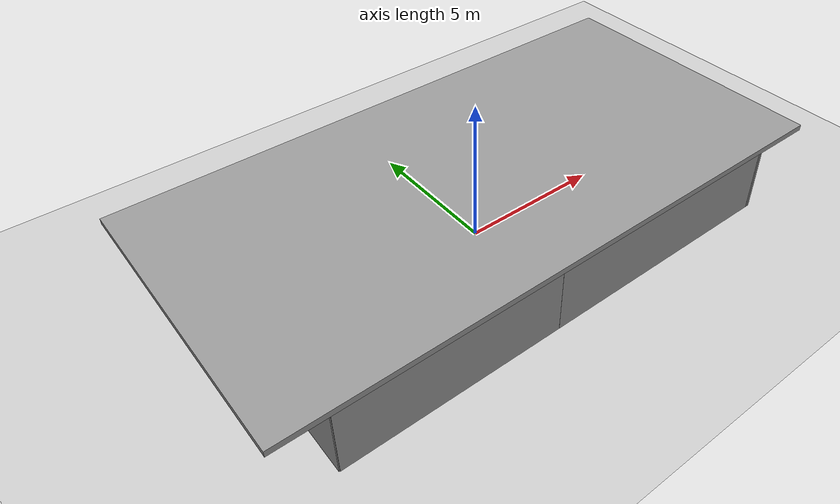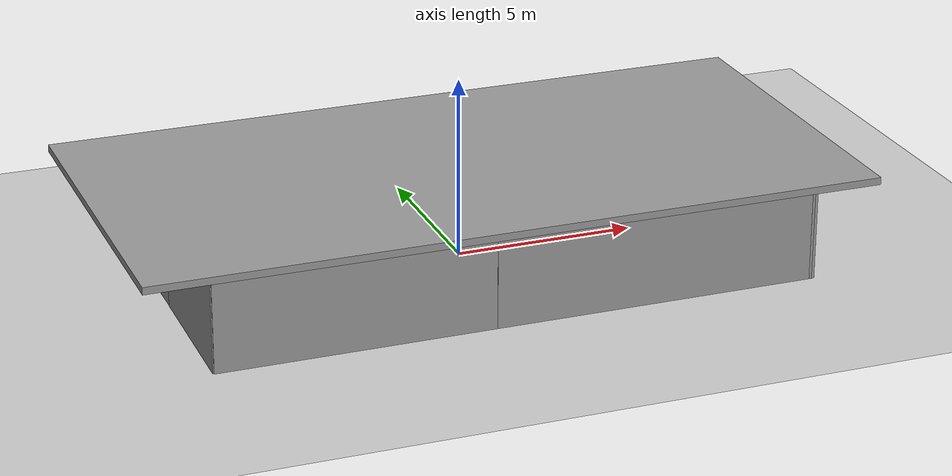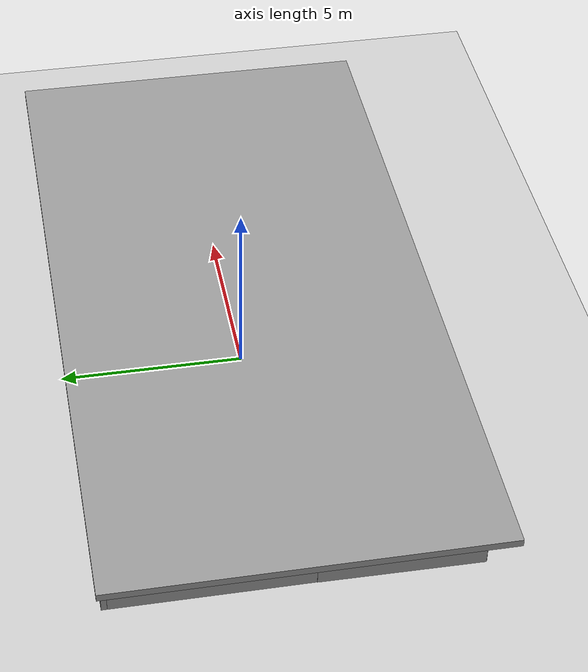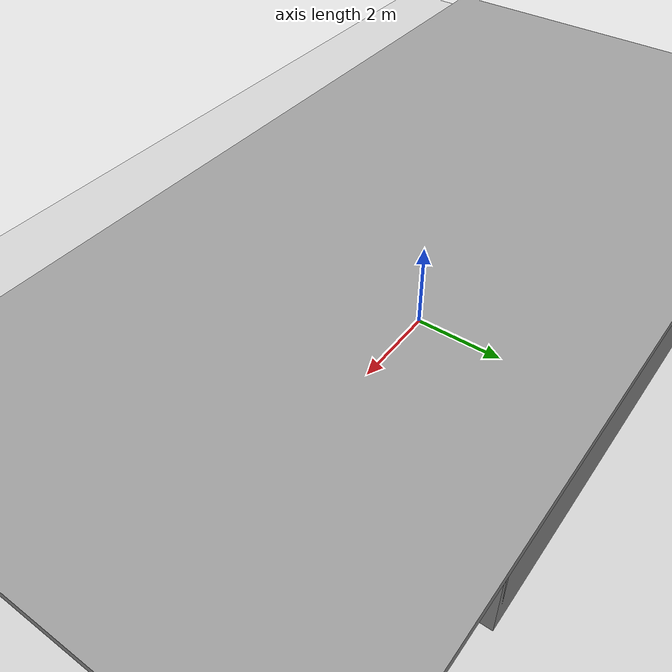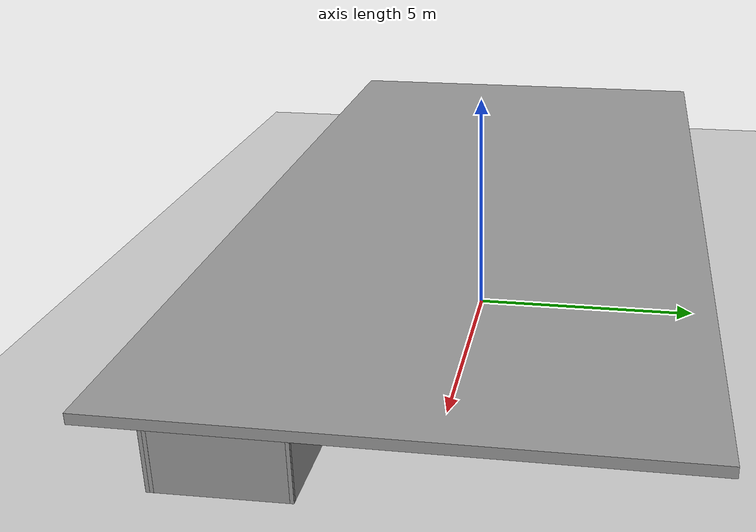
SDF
<sdf version="1.6">
 <world name="default">
  <atmosphere type="adiabatic"/>
  <wind><linear_velocity>0 0 0</linear_velocity></wind>
  <physics name="default_physics" default="1" type="ode">
   <max_step_size>0.001</max_step_size>
   <real_time_factor>1.0</real_time_factor>
   <real_time_update_rate>1000.0</real_time_update_rate>
   <max_contacts>20</max_contacts>
   <ode>
    <solver>
     <min_step_size>0.0001</min_step_size>
     <iters>50</iters>
     <sor>1.3</sor>
     <type>quick</type>
     <precon_iters>0</precon_iters>
     <use_dynamic_moi_rescaling>0</use_dynamic_moi_rescaling>
     <friction_model>pyramid_model</friction_model>
    </solver>
    <constraints>
     <cfm>0.0</cfm>
     <erp>0.2</erp>
     <contact_surface_layer>0.001</contact_surface_layer>
     <contact_max_correcting_vel>100.0</contact_max_correcting_vel>
    </constraints>
   </ode>
  </physics>
  <gravity>0 0 -9.8</gravity>
  <model name="demo_clean">
   <static>1</static>
   <link name="Wall_0">
    <collision name="Wall_0_Collision">
     <geometry><box><size>5.5 0.15 2.5</size></box></geometry>
     <pose>0 0 1.25 0 -0 0</pose>
     <surface>
      <friction>
       <ode><mu>1.0</mu><mu2>1.0</mu2><fdir1>0 0 0</fdir1><slip1>0.0</slip1><slip2>0.0</slip2></ode>
       <torsional>
        <coefficient>1.0</coefficient>
        <patch_radius>0.0</patch_radius>
        <surface_radius>0.0</surface_radius>
        <use_patch_radius>1</use_patch_radius>
        <ode><slip>0.0</slip></ode>
       </torsional>
      </friction>
      <bounce><restitution_coefficient>0.0</restitution_coefficient><threshold>1000000.0</threshold></bounce>
      <contact>
       <collide_without_contact>0</collide_without_contact>
       <collide_without_contact_bitmask>1</collide_without_contact_bitmask>
       <collide_bitmask>1</collide_bitmask>
       <ode>
        <soft_cfm>0.0</soft_cfm>
        <soft_erp>0.2</soft_erp>
        <kp>10000000000000.0</kp>
        <kd>1.0</kd>
        <max_vel>0.01</max_vel>
        <min_depth>0.0</min_depth>
       </ode>
       <bullet>
        <split_impulse>1</split_impulse>
        <split_impulse_penetration_threshold>-0.01</split_impulse_penetration_threshold>
        <soft_cfm>0.0</soft_cfm>
        <soft_erp>0.2</soft_erp>
        <kp>10000000000000.0</kp>
        <kd>1.0</kd>
       </bullet>
      </contact>
     </surface>
    </collision>
    <visual name="Wall_0_Visual">
     <geometry><box><size>5.5 0.15 2.5</size></box></geometry>
     <material>
      <script><name>Gazebo/Grey</name><uri>file://media/materials/scripts/gazebo.material</uri></script>
      <ambient>1 1 1 1</ambient>
      <shader type="pixel"><normal_map>default</normal_map></shader>
     </material>
     <pose>0 0 1.25 0 -0 0</pose>
     <transparency>0.0</transparency>
    </visual>
    <pose>-8.14649 2.06618 0 0 0 -1.5708</pose>
   </link>
   <link name="Wall_1">
    <collision name="Wall_1_Collision">
     <geometry><box><size>4.27044 0.15 2.5</size></box></geometry>
     <pose>0 0 1.25 0 -0 0</pose>
     <surface>
      <friction>
       <ode><mu>1.0</mu><mu2>1.0</mu2><fdir1>0 0 0</fdir1><slip1>0.0</slip1><slip2>0.0</slip2></ode>
       <torsional>
        <coefficient>1.0</coefficient>
        <patch_radius>0.0</patch_radius>
        <surface_radius>0.0</surface_radius>
        <use_patch_radius>1</use_patch_radius>
        <ode><slip>0.0</slip></ode>
       </torsional>
      </friction>
      <bounce><restitution_coefficient>0.0</restitution_coefficient><threshold>1000000.0</threshold></bounce>
      <contact>
       <collide_without_contact>0</collide_without_contact>
       <collide_without_contact_bitmask>1</collide_without_contact_bitmask>
       <collide_bitmask>1</collide_bitmask>
       <ode>
        <soft_cfm>0.0</soft_cfm>
        <soft_erp>0.2</soft_erp>
        <kp>10000000000000.0</kp>
        <kd>1.0</kd>
        <max_vel>0.01</max_vel>
        <min_depth>0.0</min_depth>
       </ode>
       <bullet>
        <split_impulse>1</split_impulse>
        <split_impulse_penetration_threshold>-0.01</split_impulse_penetration_threshold>
        <soft_cfm>0.0</soft_cfm>
        <soft_erp>0.2</soft_erp>
        <kp>10000000000000.0</kp>
        <kd>1.0</kd>
       </bullet>
      </contact>
     </surface>
    </collision>
    <visual name="Wall_1_Visual">
     <geometry><box><size>4.27044 0.15 2.5</size></box></geometry>
     <material>
      <script><name>Gazebo/Grey</name><uri>file://media/materials/scripts/gazebo.material</uri></script>
      <ambient>1 1 1 1</ambient>
      <shader type="pixel"><normal_map>default</normal_map></shader>
     </material>
     <pose>0 0 1.25 0 -0 0</pose>
     <transparency>0.0</transparency>
    </visual>
    <pose>-8.17617 -2.66151 0 0 0 -1.58051</pose>
   </link>
   <link name="Wall_10">
    <collision name="Wall_10_Collision">
     <geometry><box><size>3 0.15 2.5</size></box></geometry>
     <pose>0 0 1.25 0 -0 0</pose>
     <surface>
      <friction>
       <ode><mu>1.0</mu><mu2>1.0</mu2><fdir1>0 0 0</fdir1><slip1>0.0</slip1><slip2>0.0</slip2></ode>
       <torsional>
        <coefficient>1.0</coefficient>
        <patch_radius>0.0</patch_radius>
        <surface_radius>0.0</surface_radius>
        <use_patch_radius>1</use_patch_radius>
        <ode><slip>0.0</slip></ode>
       </torsional>
      </friction>
      <bounce><restitution_coefficient>0.0</restitution_coefficient><threshold>1000000.0</threshold></bounce>
      <contact>
       <collide_without_contact>0</collide_without_contact>
       <collide_without_contact_bitmask>1</collide_without_contact_bitmask>
       <collide_bitmask>1</collide_bitmask>
       <ode>
        <soft_cfm>0.0</soft_cfm>
        <soft_erp>0.2</soft_erp>
        <kp>10000000000000.0</kp>
        <kd>1.0</kd>
        <max_vel>0.01</max_vel>
        <min_depth>0.0</min_depth>
       </ode>
       <bullet>
        <split_impulse>1</split_impulse>
        <split_impulse_penetration_threshold>-0.01</split_impulse_penetration_threshold>
        <soft_cfm>0.0</soft_cfm>
        <soft_erp>0.2</soft_erp>
        <kp>10000000000000.0</kp>
        <kd>1.0</kd>
       </bullet>
      </contact>
     </surface>
    </collision>
    <visual name="Wall_10_Visual">
     <geometry><box><size>3 0.15 2.5</size></box></geometry>
     <material>
      <script><name>Gazebo/Grey</name><uri>file://media/materials/scripts/gazebo.material</uri></script>
      <ambient>1 1 1 1</ambient>
      <shader type="pixel"><normal_map>default</normal_map></shader>
     </material>
     <pose>0 0 1.25 0 -0 0</pose>
     <transparency>0.0</transparency>
    </visual>
    <pose>5.30351 3.31618 0 0 0 -1.5708</pose>
   </link>
   <link name="Wall_11">
    <collision name="Wall_11_Collision">
     <geometry><box><size>4 0.15 2.5</size></box></geometry>
     <pose>0 0 1.25 0 -0 0</pose>
     <surface>
      <friction>
       <ode><mu>1.0</mu><mu2>1.0</mu2><fdir1>0 0 0</fdir1><slip1>0.0</slip1><slip2>0.0</slip2></ode>
       <torsional>
        <coefficient>1.0</coefficient>
        <patch_radius>0.0</patch_radius>
        <surface_radius>0.0</surface_radius>
        <use_patch_radius>1</use_patch_radius>
        <ode><slip>0.0</slip></ode>
       </torsional>
      </friction>
      <bounce><restitution_coefficient>0.0</restitution_coefficient><threshold>1000000.0</threshold></bounce>
      <contact>
       <collide_without_contact>0</collide_without_contact>
       <collide_without_contact_bitmask>1</collide_without_contact_bitmask>
       <collide_bitmask>1</collide_bitmask>
       <ode>
        <soft_cfm>0.0</soft_cfm>
        <soft_erp>0.2</soft_erp>
        <kp>10000000000000.0</kp>
        <kd>1.0</kd>
        <max_vel>0.01</max_vel>
        <min_depth>0.0</min_depth>
       </ode>
       <bullet>
        <split_impulse>1</split_impulse>
        <split_impulse_penetration_threshold>-0.01</split_impulse_penetration_threshold>
        <soft_cfm>0.0</soft_cfm>
        <soft_erp>0.2</soft_erp>
        <kp>10000000000000.0</kp>
        <kd>1.0</kd>
       </bullet>
      </contact>
     </surface>
    </collision>
    <visual name="Wall_11_Visual">
     <geometry><box><size>4 0.15 2.5</size></box></geometry>
     <material>
      <script><name>Gazebo/Grey</name><uri>file://media/materials/scripts/gazebo.material</uri></script>
      <ambient>1 1 1 1</ambient>
      <shader type="pixel"><normal_map>default</normal_map></shader>
     </material>
     <pose>0 0 1.25 0 -0 0</pose>
     <transparency>0.0</transparency>
    </visual>
    <pose>3.37851 1.89118 0 0 -0 3.14159</pose>
   </link>
   <link name="Wall_13">
    <collision name="Wall_13_Collision">
     <geometry><box><size>4.25 0.15 2.5</size></box></geometry>
     <pose>0 0 1.25 0 -0 0</pose>
     <surface>
      <friction>
       <ode><mu>1.0</mu><mu2>1.0</mu2><fdir1>0 0 0</fdir1><slip1>0.0</slip1><slip2>0.0</slip2></ode>
       <torsional>
        <coefficient>1.0</coefficient>
        <patch_radius>0.0</patch_radius>
        <surface_radius>0.0</surface_radius>
        <use_patch_radius>1</use_patch_radius>
        <ode><slip>0.0</slip></ode>
       </torsional>
      </friction>
      <bounce><restitution_coefficient>0.0</restitution_coefficient><threshold>1000000.0</threshold></bounce>
      <contact>
       <collide_without_contact>0</collide_without_contact>
       <collide_without_contact_bitmask>1</collide_without_contact_bitmask>
       <collide_bitmask>1</collide_bitmask>
       <ode>
        <soft_cfm>0.0</soft_cfm>
        <soft_erp>0.2</soft_erp>
        <kp>10000000000000.0</kp>
        <kd>1.0</kd>
        <max_vel>0.01</max_vel>
        <min_depth>0.0</min_depth>
       </ode>
       <bullet>
        <split_impulse>1</split_impulse>
        <split_impulse_penetration_threshold>-0.01</split_impulse_penetration_threshold>
        <soft_cfm>0.0</soft_cfm>
        <soft_erp>0.2</soft_erp>
        <kp>10000000000000.0</kp>
        <kd>1.0</kd>
       </bullet>
      </contact>
     </surface>
    </collision>
    <visual name="Wall_13_Visual">
     <geometry><box><size>4.25 0.15 2.5</size></box></geometry>
     <material>
      <script><name>Gazebo/Grey</name><uri>file://media/materials/scripts/gazebo.material</uri></script>
      <ambient>1 1 1 1</ambient>
      <shader type="pixel"><normal_map>default</normal_map></shader>
     </material>
     <pose>0 0 1.25 0 -0 0</pose>
     <transparency>0.0</transparency>
    </visual>
    <pose>5.30351 -0.158824 0 0 0 -1.5708</pose>
   </link>
   <link name="Wall_14">
    <collision name="Wall_14_Collision">
     <geometry><box><size>3 0.15 2.5</size></box></geometry>
     <pose>0 0 1.25 0 -0 0</pose>
     <surface>
      <friction>
       <ode><mu>1.0</mu><mu2>1.0</mu2><fdir1>0 0 0</fdir1><slip1>0.0</slip1><slip2>0.0</slip2></ode>
       <torsional>
        <coefficient>1.0</coefficient>
        <patch_radius>0.0</patch_radius>
        <surface_radius>0.0</surface_radius>
        <use_patch_radius>1</use_patch_radius>
        <ode><slip>0.0</slip></ode>
       </torsional>
      </friction>
      <bounce><restitution_coefficient>0.0</restitution_coefficient><threshold>1000000.0</threshold></bounce>
      <contact>
       <collide_without_contact>0</collide_without_contact>
       <collide_without_contact_bitmask>1</collide_without_contact_bitmask>
       <collide_bitmask>1</collide_bitmask>
       <ode>
        <soft_cfm>0.0</soft_cfm>
        <soft_erp>0.2</soft_erp>
        <kp>10000000000000.0</kp>
        <kd>1.0</kd>
        <max_vel>0.01</max_vel>
        <min_depth>0.0</min_depth>
       </ode>
       <bullet>
        <split_impulse>1</split_impulse>
        <split_impulse_penetration_threshold>-0.01</split_impulse_penetration_threshold>
        <soft_cfm>0.0</soft_cfm>
        <soft_erp>0.2</soft_erp>
        <kp>10000000000000.0</kp>
        <kd>1.0</kd>
       </bullet>
      </contact>
     </surface>
    </collision>
    <visual name="Wall_14_Visual">
     <geometry><box><size>3 0.15 2.5</size></box></geometry>
     <material>
      <script><name>Gazebo/Grey</name><uri>file://media/materials/scripts/gazebo.material</uri></script>
      <ambient>1 1 1 1</ambient>
      <shader type="pixel"><normal_map>default</normal_map></shader>
     </material>
     <pose>0 0 1.25 0 -0 0</pose>
     <transparency>0.0</transparency>
    </visual>
    <pose>6.72851 -2.20882 0 0 -0 0</pose>
   </link>
   <link name="Wall_15">
    <collision name="Wall_15_Collision">
     <geometry><box><size>2.6816 0.15 2.5</size></box></geometry>
     <pose>0 0 1.25 0 -0 0</pose>
     <surface>
      <friction>
       <ode><mu>1.0</mu><mu2>1.0</mu2><fdir1>0 0 0</fdir1><slip1>0.0</slip1><slip2>0.0</slip2></ode>
       <torsional>
        <coefficient>1.0</coefficient>
        <patch_radius>0.0</patch_radius>
        <surface_radius>0.0</surface_radius>
        <use_patch_radius>1</use_patch_radius>
        <ode><slip>0.0</slip></ode>
       </torsional>
      </friction>
      <bounce><restitution_coefficient>0.0</restitution_coefficient><threshold>1000000.0</threshold></bounce>
      <contact>
       <collide_without_contact>0</collide_without_contact>
       <collide_without_contact_bitmask>1</collide_without_contact_bitmask>
       <collide_bitmask>1</collide_bitmask>
       <ode>
        <soft_cfm>0.0</soft_cfm>
        <soft_erp>0.2</soft_erp>
        <kp>10000000000000.0</kp>
        <kd>1.0</kd>
        <max_vel>0.01</max_vel>
        <min_depth>0.0</min_depth>
       </ode>
       <bullet>
        <split_impulse>1</split_impulse>
        <split_impulse_penetration_threshold>-0.01</split_impulse_penetration_threshold>
        <soft_cfm>0.0</soft_cfm>
        <soft_erp>0.2</soft_erp>
        <kp>10000000000000.0</kp>
        <kd>1.0</kd>
       </bullet>
      </contact>
     </surface>
    </collision>
    <visual name="Wall_15_Visual">
     <geometry><box><size>2.6816 0.15 2.5</size></box></geometry>
     <material>
      <script><name>Gazebo/Grey</name><uri>file://media/materials/scripts/gazebo.material</uri></script>
      <ambient>1 1 1 1</ambient>
      <shader type="pixel"><normal_map>default</normal_map></shader>
     </material>
     <pose>0 0 1.25 0 -0 0</pose>
     <transparency>0.0</transparency>
    </visual>
    <pose>8.16988 -3.47452 0 0 0 -1.55787</pose>
   </link>
   <link name="Wall_16">
    <collision name="Wall_16_Collision">
     <geometry><box><size>9 0.15 2.5</size></box></geometry>
     <pose>0 0 1.25 0 -0 0</pose>
     <surface>
      <friction>
       <ode><mu>1.0</mu><mu2>1.0</mu2><fdir1>0 0 0</fdir1><slip1>0.0</slip1><slip2>0.0</slip2></ode>
       <torsional>
        <coefficient>1.0</coefficient>
        <patch_radius>0.0</patch_radius>
        <surface_radius>0.0</surface_radius>
        <use_patch_radius>1</use_patch_radius>
        <ode><slip>0.0</slip></ode>
       </torsional>
      </friction>
      <bounce><restitution_coefficient>0.0</restitution_coefficient><threshold>1000000.0</threshold></bounce>
      <contact>
       <collide_without_contact>0</collide_without_contact>
       <collide_without_contact_bitmask>1</collide_without_contact_bitmask>
       <collide_bitmask>1</collide_bitmask>
       <ode>
        <soft_cfm>0.0</soft_cfm>
        <soft_erp>0.2</soft_erp>
        <kp>10000000000000.0</kp>
        <kd>1.0</kd>
        <max_vel>0.01</max_vel>
        <min_depth>0.0</min_depth>
       </ode>
       <bullet>
        <split_impulse>1</split_impulse>
        <split_impulse_penetration_threshold>-0.01</split_impulse_penetration_threshold>
        <soft_cfm>0.0</soft_cfm>
        <soft_erp>0.2</soft_erp>
        <kp>10000000000000.0</kp>
        <kd>1.0</kd>
       </bullet>
      </contact>
     </surface>
    </collision>
    <visual name="Wall_16_Visual">
     <geometry><box><size>9 0.15 2.5</size></box></geometry>
     <material>
      <script><name>Gazebo/Grey</name><uri>file://media/materials/scripts/gazebo.material</uri></script>
      <ambient>1 1 1 1</ambient>
      <shader type="pixel"><normal_map>default</normal_map></shader>
     </material>
     <pose>0 0 1.25 0 -0 0</pose>
     <transparency>0.0</transparency>
    </visual>
    <pose>3.76125 -4.74021 0 0 -0 3.14159</pose>
   </link>
   <link name="Wall_19">
    <collision name="Wall_19_Collision">
     <geometry><box><size>2.34163 0.15 2.5</size></box></geometry>
     <pose>0 0 1.25 0 -0 0</pose>
     <surface>
      <friction>
       <ode><mu>1.0</mu><mu2>1.0</mu2><fdir1>0 0 0</fdir1><slip1>0.0</slip1><slip2>0.0</slip2></ode>
       <torsional>
        <coefficient>1.0</coefficient>
        <patch_radius>0.0</patch_radius>
        <surface_radius>0.0</surface_radius>
        <use_patch_radius>1</use_patch_radius>
        <ode><slip>0.0</slip></ode>
       </torsional>
      </friction>
      <bounce><restitution_coefficient>0.0</restitution_coefficient><threshold>1000000.0</threshold></bounce>
      <contact>
       <collide_without_contact>0</collide_without_contact>
       <collide_without_contact_bitmask>1</collide_without_contact_bitmask>
       <collide_bitmask>1</collide_bitmask>
       <ode>
        <soft_cfm>0.0</soft_cfm>
        <soft_erp>0.2</soft_erp>
        <kp>10000000000000.0</kp>
        <kd>1.0</kd>
        <max_vel>0.01</max_vel>
        <min_depth>0.0</min_depth>
       </ode>
       <bullet>
        <split_impulse>1</split_impulse>
        <split_impulse_penetration_threshold>-0.01</split_impulse_penetration_threshold>
        <soft_cfm>0.0</soft_cfm>
        <soft_erp>0.2</soft_erp>
        <kp>10000000000000.0</kp>
        <kd>1.0</kd>
       </bullet>
      </contact>
     </surface>
    </collision>
    <visual name="Wall_19_Visual">
     <geometry><box><size>2.34163 0.15 2.5</size></box></geometry>
     <material>
      <script><name>Gazebo/Grey</name><uri>file://media/materials/scripts/gazebo.material</uri></script>
      <ambient>1 1 1 1</ambient>
      <shader type="pixel"><normal_map>default</normal_map></shader>
     </material>
     <pose>0 0 1.25 0 -0 0</pose>
     <transparency>0.0</transparency>
    </visual>
    <inertial>
     <inertia><ixx>0.0</ixx><iyy>0.0</iyy><izz>0.0</izz><ixy>0.0</ixy><ixz>0.0</ixz><iyz>0.0</iyz></inertia>
     <mass>1.0</mass>
    </inertial>
    <pose>0.295923 -2.24288 0 0 -0 0</pose>
   </link>
   <link name="Wall_2">
    <collision name="Wall_2_Collision">
     <geometry><box><size>7.5 0.15 2.5</size></box></geometry>
     <pose>0 0 1.25 0 -0 0</pose>
     <surface>
      <friction>
       <ode><mu>1.0</mu><mu2>1.0</mu2><fdir1>0 0 0</fdir1><slip1>0.0</slip1><slip2>0.0</slip2></ode>
       <torsional>
        <coefficient>1.0</coefficient>
        <patch_radius>0.0</patch_radius>
        <surface_radius>0.0</surface_radius>
        <use_patch_radius>1</use_patch_radius>
        <ode><slip>0.0</slip></ode>
       </torsional>
      </friction>
      <bounce><restitution_coefficient>0.0</restitution_coefficient><threshold>1000000.0</threshold></bounce>
      <contact>
       <collide_without_contact>0</collide_without_contact>
       <collide_without_contact_bitmask>1</collide_without_contact_bitmask>
       <collide_bitmask>1</collide_bitmask>
       <ode>
        <soft_cfm>0.0</soft_cfm>
        <soft_erp>0.2</soft_erp>
        <kp>10000000000000.0</kp>
        <kd>1.0</kd>
        <max_vel>0.01</max_vel>
        <min_depth>0.0</min_depth>
       </ode>
       <bullet>
        <split_impulse>1</split_impulse>
        <split_impulse_penetration_threshold>-0.01</split_impulse_penetration_threshold>
        <soft_cfm>0.0</soft_cfm>
        <soft_erp>0.2</soft_erp>
        <kp>10000000000000.0</kp>
        <kd>1.0</kd>
       </bullet>
      </contact>
     </surface>
    </collision>
    <visual name="Wall_2_Visual">
     <geometry><box><size>7.5 0.15 2.5</size></box></geometry>
     <material>
      <script><name>Gazebo/Grey</name><uri>file://media/materials/scripts/gazebo.material</uri></script>
      <ambient>1 1 1 1</ambient>
      <shader type="pixel"><normal_map>default</normal_map></shader>
     </material>
     <pose>0 0 1.25 0 -0 0</pose>
     <transparency>0.0</transparency>
    </visual>
    <pose>-4.49149 -4.74 0 0 -0 0</pose>
   </link>
   <link name="Wall_21">
    <collision name="Wall_21_Collision">
     <geometry><box><size>2.5 0.15 2.5</size></box></geometry>
     <pose>0 0 1.25 0 -0 0</pose>
     <surface>
      <friction>
       <ode><mu>1.0</mu><mu2>1.0</mu2><fdir1>0 0 0</fdir1><slip1>0.0</slip1><slip2>0.0</slip2></ode>
       <torsional>
        <coefficient>1.0</coefficient>
        <patch_radius>0.0</patch_radius>
        <surface_radius>0.0</surface_radius>
        <use_patch_radius>1</use_patch_radius>
        <ode><slip>0.0</slip></ode>
       </torsional>
      </friction>
      <bounce><restitution_coefficient>0.0</restitution_coefficient><threshold>1000000.0</threshold></bounce>
      <contact>
       <collide_without_contact>0</collide_without_contact>
       <collide_without_contact_bitmask>1</collide_without_contact_bitmask>
       <collide_bitmask>1</collide_bitmask>
       <ode>
        <soft_cfm>0.0</soft_cfm>
        <soft_erp>0.2</soft_erp>
        <kp>10000000000000.0</kp>
        <kd>1.0</kd>
        <max_vel>0.01</max_vel>
        <min_depth>0.0</min_depth>
       </ode>
       <bullet>
        <split_impulse>1</split_impulse>
        <split_impulse_penetration_threshold>-0.01</split_impulse_penetration_threshold>
        <soft_cfm>0.0</soft_cfm>
        <soft_erp>0.2</soft_erp>
        <kp>10000000000000.0</kp>
        <kd>1.0</kd>
       </bullet>
      </contact>
     </surface>
    </collision>
    <visual name="Wall_21_Visual">
     <geometry><box><size>2.5 0.15 2.5</size></box></geometry>
     <material>
      <script><name>Gazebo/Grey</name><uri>file://media/materials/scripts/gazebo.material</uri></script>
      <ambient>1 1 1 1</ambient>
      <shader type="pixel"><normal_map>default</normal_map></shader>
     </material>
     <pose>0 0 1.25 0 -0 0</pose>
     <transparency>0.0</transparency>
    </visual>
    <pose>0.573753 -3.46553 0 0 0 -1.5708</pose>
   </link>
   <link name="Wall_21_clone">
    <collision name="Wall_21_Collision">
     <geometry><box><size>0.240964 0.15 2.5</size></box></geometry>
     <pose>0 0 1.25 0 -0 0</pose>
     <surface>
      <friction>
       <ode><mu>1.0</mu><mu2>1.0</mu2><fdir1>0 0 0</fdir1><slip1>0.0</slip1><slip2>0.0</slip2></ode>
       <torsional>
        <coefficient>1.0</coefficient>
        <patch_radius>0.0</patch_radius>
        <surface_radius>0.0</surface_radius>
        <use_patch_radius>1</use_patch_radius>
        <ode><slip>0.0</slip></ode>
       </torsional>
      </friction>
      <bounce><restitution_coefficient>0.0</restitution_coefficient><threshold>1000000.0</threshold></bounce>
      <contact>
       <collide_without_contact>0</collide_without_contact>
       <collide_without_contact_bitmask>1</collide_without_contact_bitmask>
       <collide_bitmask>1</collide_bitmask>
       <ode>
        <soft_cfm>0.0</soft_cfm>
        <soft_erp>0.2</soft_erp>
        <kp>10000000000000.0</kp>
        <kd>1.0</kd>
        <max_vel>0.01</max_vel>
        <min_depth>0.0</min_depth>
       </ode>
       <bullet>
        <split_impulse>1</split_impulse>
        <split_impulse_penetration_threshold>-0.01</split_impulse_penetration_threshold>
        <soft_cfm>0.0</soft_cfm>
        <soft_erp>0.2</soft_erp>
        <kp>10000000000000.0</kp>
        <kd>1.0</kd>
       </bullet>
      </contact>
     </surface>
    </collision>
    <visual name="Wall_21_Visual">
     <geometry><box><size>0.240964 0.15 2.5</size></box></geometry>
     <material>
      <script><name>Gazebo/Grey</name><uri>file://media/materials/scripts/gazebo.material</uri></script>
      <ambient>1 1 1 1</ambient>
      <shader type="pixel"><normal_map>default</normal_map></shader>
     </material>
     <pose>0 0 1.25 0 -0 0</pose>
     <transparency>0.0</transparency>
    </visual>
    <inertial>
     <inertia><ixx>0.0</ixx><iyy>0.0</iyy><izz>0.0</izz><ixy>0.0</ixy><ixz>0.0</ixz><iyz>0.0</iyz></inertia>
     <mass>1.0</mass>
    </inertial>
    <pose>-0.802658 -0.717313 0 0 0 -1.5708</pose>
   </link>
   <link name="Wall_21_clone_0">
    <collision name="Wall_21_Collision">
     <geometry><box><size>0.394105 0.15 2.5</size></box></geometry>
     <pose>0 0 1.25 0 -0 0</pose>
     <surface>
      <friction>
       <ode><mu>1.0</mu><mu2>1.0</mu2><fdir1>0 0 0</fdir1><slip1>0.0</slip1><slip2>0.0</slip2></ode>
       <torsional>
        <coefficient>1.0</coefficient>
        <patch_radius>0.0</patch_radius>
        <surface_radius>0.0</surface_radius>
        <use_patch_radius>1</use_patch_radius>
        <ode><slip>0.0</slip></ode>
       </torsional>
      </friction>
      <bounce><restitution_coefficient>0.0</restitution_coefficient><threshold>1000000.0</threshold></bounce>
      <contact>
       <collide_without_contact>0</collide_without_contact>
       <collide_without_contact_bitmask>1</collide_without_contact_bitmask>
       <collide_bitmask>1</collide_bitmask>
       <ode>
        <soft_cfm>0.0</soft_cfm>
        <soft_erp>0.2</soft_erp>
        <kp>10000000000000.0</kp>
        <kd>1.0</kd>
        <max_vel>0.01</max_vel>
        <min_depth>0.0</min_depth>
       </ode>
       <bullet>
        <split_impulse>1</split_impulse>
        <split_impulse_penetration_threshold>-0.01</split_impulse_penetration_threshold>
        <soft_cfm>0.0</soft_cfm>
        <soft_erp>0.2</soft_erp>
        <kp>10000000000000.0</kp>
        <kd>1.0</kd>
       </bullet>
      </contact>
     </surface>
    </collision>
    <visual name="Wall_21_Visual">
     <geometry><box><size>0.394105 0.15 2.5</size></box></geometry>
     <material>
      <script><name>Gazebo/Grey</name><uri>file://media/materials/scripts/gazebo.material</uri></script>
      <ambient>1 1 1 1</ambient>
      <shader type="pixel"><normal_map>default</normal_map></shader>
     </material>
     <pose>0 0 1.25 0 -0 0</pose>
     <transparency>0.0</transparency>
    </visual>
    <inertial>
     <inertia><ixx>0.0</ixx><iyy>0.0</iyy><izz>0.0</izz><ixy>0.0</ixy><ixz>0.0</ixz><iyz>0.0</iyz></inertia>
     <mass>1.0</mass>
    </inertial>
    <pose>-0.820336 -2.26773 0 0 0 -1.5708</pose>
   </link>
   <link name="Wall_21_clone_0_clone_0_clone_clone">
    <gravity>0</gravity>
    <collision name="Wall_21_Collision">
     <geometry><box><size>1.1941 0.15 1.96033</size></box></geometry>
     <pose>0 0 1.25 0 -0 0</pose>
     <surface>
      <friction>
       <ode><mu>1.0</mu><mu2>1.0</mu2><fdir1>0 0 0</fdir1><slip1>0.0</slip1><slip2>0.0</slip2></ode>
       <torsional>
        <coefficient>1.0</coefficient>
        <patch_radius>0.0</patch_radius>
        <surface_radius>0.0</surface_radius>
        <use_patch_radius>1</use_patch_radius>
        <ode><slip>0.0</slip></ode>
       </torsional>
      </friction>
      <bounce><restitution_coefficient>0.0</restitution_coefficient><threshold>1000000.0</threshold></bounce>
      <contact>
       <collide_without_contact>0</collide_without_contact>
       <collide_without_contact_bitmask>1</collide_without_contact_bitmask>
       <collide_bitmask>1</collide_bitmask>
       <ode>
        <soft_cfm>0.0</soft_cfm>
        <soft_erp>0.2</soft_erp>
        <kp>10000000000000.0</kp>
        <kd>1.0</kd>
        <max_vel>0.01</max_vel>
        <min_depth>0.0</min_depth>
       </ode>
       <bullet>
        <split_impulse>1</split_impulse>
        <split_impulse_penetration_threshold>-0.01</split_impulse_penetration_threshold>
        <soft_cfm>0.0</soft_cfm>
        <soft_erp>0.2</soft_erp>
        <kp>10000000000000.0</kp>
        <kd>1.0</kd>
       </bullet>
      </contact>
     </surface>
    </collision>
    <visual name="Wall_21_Visual">
     <geometry><box><size>1.1941 0.15 1.96033</size></box></geometry>
     <material>
      <script><name>Gazebo/Grey</name><uri>file://media/materials/scripts/gazebo.material</uri></script>
      <ambient>1 1 1 1</ambient>
      <shader type="pixel"><normal_map>__default__</normal_map></shader>
      <diffuse>0.7 0.7 0.7 1.0</diffuse>
      <specular>0.01 0.01 0.01 1</specular>
      <emissive>0 0 0 1</emissive>
     </material>
     <pose>0 0 1.25 0 -0 0</pose>
     <transparency>0.0</transparency>
    </visual>
    <inertial>
     <inertia><ixx>0.0</ixx><iyy>0.0</iyy><izz>0.0</izz><ixy>0.0</ixy><ixz>0.0</ixz><iyz>0.0</iyz></inertia>
     <mass>1.0</mass>
    </inertial>
    <pose>-1.47342 -0.839052 -0.23202 0 -0 3.0297</pose>
   </link>
   <link name="Wall_21_clone_0_clone_0_clone_clone_clone_clone">
    <gravity>0</gravity>
    <collision name="Wall_21_Collision">
     <geometry><box><size>0.924919 0.15 1.96033</size></box></geometry>
     <pose>0 0 1.25 0 -0 0</pose>
     <surface>
      <friction>
       <ode><mu>1.0</mu><mu2>1.0</mu2><fdir1>0 0 0</fdir1><slip1>0.0</slip1><slip2>0.0</slip2></ode>
       <torsional>
        <coefficient>1.0</coefficient>
        <patch_radius>0.0</patch_radius>
        <surface_radius>0.0</surface_radius>
        <use_patch_radius>1</use_patch_radius>
        <ode><slip>0.0</slip></ode>
       </torsional>
      </friction>
      <bounce><restitution_coefficient>0.0</restitution_coefficient><threshold>1000000.0</threshold></bounce>
      <contact>
       <collide_without_contact>0</collide_without_contact>
       <collide_without_contact_bitmask>1</collide_without_contact_bitmask>
       <collide_bitmask>1</collide_bitmask>
       <ode>
        <soft_cfm>0.0</soft_cfm>
        <soft_erp>0.2</soft_erp>
        <kp>10000000000000.0</kp>
        <kd>1.0</kd>
        <max_vel>0.01</max_vel>
        <min_depth>0.0</min_depth>
       </ode>
       <bullet>
        <split_impulse>1</split_impulse>
        <split_impulse_penetration_threshold>-0.01</split_impulse_penetration_threshold>
        <soft_cfm>0.0</soft_cfm>
        <soft_erp>0.2</soft_erp>
        <kp>10000000000000.0</kp>
        <kd>1.0</kd>
       </bullet>
      </contact>
     </surface>
    </collision>
    <visual name="Wall_21_Visual">
     <geometry><box><size>0.924919 0.15 1.96033</size></box></geometry>
     <material>
      <script><name>Gazebo/Grey</name><uri>file://media/materials/scripts/gazebo.material</uri></script>
      <ambient>1 1 1 1</ambient>
      <shader type="pixel"><normal_map>__default__</normal_map></shader>
      <diffuse>0.7 0.7 0.7 1.0</diffuse>
      <specular>0.01 0.01 0.01 1</specular>
      <emissive>0 0 0 1</emissive>
     </material>
     <pose>0 0 1.25 0 -0 0</pose>
     <transparency>0.0</transparency>
    </visual>
    <inertial>
     <inertia><ixx>0.0</ixx><iyy>0.0</iyy><izz>0.0</izz><ixy>0.0</ixy><ixz>0.0</ixz><iyz>0.0</iyz></inertia>
     <mass>1.0</mass>
    </inertial>
    <pose>2.0073 -0.280742 -0.23202 0 -0 2.28452</pose>
   </link>
   <link name="Wall_21_clone_0_clone_0_clone_clone_clone_clone_clone_clone_clone_clone">
    <gravity>0</gravity>
    <collision name="Wall_21_Collision">
     <geometry><box><size>0.663949 0.15 1.96033</size></box></geometry>
     <pose>0 0 1.25 0 -0 0</pose>
     <surface>
      <friction>
       <ode><mu>1.0</mu><mu2>1.0</mu2><fdir1>0 0 0</fdir1><slip1>0.0</slip1><slip2>0.0</slip2></ode>
       <torsional>
        <coefficient>1.0</coefficient>
        <patch_radius>0.0</patch_radius>
        <surface_radius>0.0</surface_radius>
        <use_patch_radius>1</use_patch_radius>
        <ode><slip>0.0</slip></ode>
       </torsional>
      </friction>
      <bounce><restitution_coefficient>0.0</restitution_coefficient><threshold>1000000.0</threshold></bounce>
      <contact>
       <collide_without_contact>0</collide_without_contact>
       <collide_without_contact_bitmask>1</collide_without_contact_bitmask>
       <collide_bitmask>1</collide_bitmask>
       <ode>
        <soft_cfm>0.0</soft_cfm>
        <soft_erp>0.2</soft_erp>
        <kp>10000000000000.0</kp>
        <kd>1.0</kd>
        <max_vel>0.01</max_vel>
        <min_depth>0.0</min_depth>
       </ode>
       <bullet>
        <split_impulse>1</split_impulse>
        <split_impulse_penetration_threshold>-0.01</split_impulse_penetration_threshold>
        <soft_cfm>0.0</soft_cfm>
        <soft_erp>0.2</soft_erp>
        <kp>10000000000000.0</kp>
        <kd>1.0</kd>
       </bullet>
      </contact>
     </surface>
    </collision>
    <visual name="Wall_21_Visual">
     <geometry><box><size>0.663949 0.15 1.96033</size></box></geometry>
     <material>
      <script><name>Gazebo/Grey</name><uri>file://media/materials/scripts/gazebo.material</uri></script>
      <ambient>1 1 1 1</ambient>
      <shader type="pixel"><normal_map>__default__</normal_map></shader>
      <diffuse>0.7 0.7 0.7 1.0</diffuse>
      <specular>0.01 0.01 0.01 1</specular>
      <emissive>0 0 0 1</emissive>
     </material>
     <pose>0 0 1.25 0 -0 0</pose>
     <transparency>0.0</transparency>
    </visual>
    <inertial>
     <inertia><ixx>0.0</ixx><iyy>0.0</iyy><izz>0.0</izz><ixy>0.0</ixy><ixz>0.0</ixz><iyz>0.0</iyz></inertia>
     <mass>1.0</mass>
    </inertial>
    <pose>3.68306 -1.18793 -0.23202 0 -0 2.79384</pose>
   </link>
   <link name="Wall_21_clone_0_clone_0_clone_clone_clone_clone_clone_clone_clone_clone_clone_clone">
    <gravity>0</gravity>
    <collision name="Wall_21_Collision">
     <geometry><box><size>0.663949 0.15 1.96033</size></box></geometry>
     <pose>0 0 1.25 0 -0 0</pose>
     <surface>
      <friction>
       <ode><mu>1.0</mu><mu2>1.0</mu2><fdir1>0 0 0</fdir1><slip1>0.0</slip1><slip2>0.0</slip2></ode>
       <torsional>
        <coefficient>1.0</coefficient>
        <patch_radius>0.0</patch_radius>
        <surface_radius>0.0</surface_radius>
        <use_patch_radius>1</use_patch_radius>
        <ode><slip>0.0</slip></ode>
       </torsional>
      </friction>
      <bounce><restitution_coefficient>0.0</restitution_coefficient><threshold>1000000.0</threshold></bounce>
      <contact>
       <collide_without_contact>0</collide_without_contact>
       <collide_without_contact_bitmask>1</collide_without_contact_bitmask>
       <collide_bitmask>1</collide_bitmask>
       <ode>
        <soft_cfm>0.0</soft_cfm>
        <soft_erp>0.2</soft_erp>
        <kp>10000000000000.0</kp>
        <kd>1.0</kd>
        <max_vel>0.01</max_vel>
        <min_depth>0.0</min_depth>
       </ode>
       <bullet>
        <split_impulse>1</split_impulse>
        <split_impulse_penetration_threshold>-0.01</split_impulse_penetration_threshold>
        <soft_cfm>0.0</soft_cfm>
        <soft_erp>0.2</soft_erp>
        <kp>10000000000000.0</kp>
        <kd>1.0</kd>
       </bullet>
      </contact>
     </surface>
    </collision>
    <visual name="Wall_21_Visual">
     <geometry><box><size>0.663949 0.15 1.96033</size></box></geometry>
     <material>
      <script><name>Gazebo/Grey</name><uri>file://media/materials/scripts/gazebo.material</uri></script>
      <ambient>1 1 1 1</ambient>
      <shader type="pixel"><normal_map>__default__</normal_map></shader>
      <diffuse>0.7 0.7 0.7 1.0</diffuse>
      <specular>0.01 0.01 0.01 1</specular>
      <emissive>0 0 0 1</emissive>
     </material>
     <pose>0 0 1.25 0 -0 0</pose>
     <transparency>0.0</transparency>
    </visual>
    <inertial>
     <inertia><ixx>0.0</ixx><iyy>0.0</iyy><izz>0.0</izz><ixy>0.0</ixy><ixz>0.0</ixz><iyz>0.0</iyz></inertia>
     <mass>1.0</mass>
    </inertial>
    <pose>3.65792 -0.364043 -0.23202 0 0 -2.77941</pose>
   </link>
   <link name="Wall_21_clone_clone">
    <collision name="Wall_21_Collision">
     <geometry><box><size>0.240964 0.15 2.5</size></box></geometry>
     <pose>0 0 1.25 0 -0 0</pose>
     <surface>
      <friction>
       <ode><mu>1.0</mu><mu2>1.0</mu2><fdir1>0 0 0</fdir1><slip1>0.0</slip1><slip2>0.0</slip2></ode>
       <torsional>
        <coefficient>1.0</coefficient>
        <patch_radius>0.0</patch_radius>
        <surface_radius>0.0</surface_radius>
        <use_patch_radius>1</use_patch_radius>
        <ode><slip>0.0</slip></ode>
       </torsional>
      </friction>
      <bounce><restitution_coefficient>0.0</restitution_coefficient><threshold>1000000.0</threshold></bounce>
      <contact>
       <collide_without_contact>0</collide_without_contact>
       <collide_without_contact_bitmask>1</collide_without_contact_bitmask>
       <collide_bitmask>1</collide_bitmask>
       <ode>
        <soft_cfm>0.0</soft_cfm>
        <soft_erp>0.2</soft_erp>
        <kp>10000000000000.0</kp>
        <kd>1.0</kd>
        <max_vel>0.01</max_vel>
        <min_depth>0.0</min_depth>
       </ode>
       <bullet>
        <split_impulse>1</split_impulse>
        <split_impulse_penetration_threshold>-0.01</split_impulse_penetration_threshold>
        <soft_cfm>0.0</soft_cfm>
        <soft_erp>0.2</soft_erp>
        <kp>10000000000000.0</kp>
        <kd>1.0</kd>
       </bullet>
      </contact>
     </surface>
    </collision>
    <visual name="Wall_21_Visual">
     <geometry><box><size>0.240964 0.15 2.5</size></box></geometry>
     <material>
      <script><name>Gazebo/Grey</name><uri>file://media/materials/scripts/gazebo.material</uri></script>
      <ambient>1 1 1 1</ambient>
      <shader type="pixel"><normal_map>default</normal_map></shader>
     </material>
     <pose>0 0 1.25 0 -0 0</pose>
     <transparency>0.0</transparency>
    </visual>
    <inertial>
     <inertia><ixx>0.0</ixx><iyy>0.0</iyy><izz>0.0</izz><ixy>0.0</ixy><ixz>0.0</ixz><iyz>0.0</iyz></inertia>
     <mass>1.0</mass>
    </inertial>
    <pose>-0.824993 -4.62184 0 0 0 -1.5708</pose>
   </link>
   <link name="Wall_23">
    <collision name="Wall_23_Collision">
     <geometry><box><size>0.981708 0.15 2.5</size></box></geometry>
     <pose>0 0 1.25 0 -0 0</pose>
     <surface>
      <friction>
       <ode><mu>1.0</mu><mu2>1.0</mu2><fdir1>0 0 0</fdir1><slip1>0.0</slip1><slip2>0.0</slip2></ode>
       <torsional>
        <coefficient>1.0</coefficient>
        <patch_radius>0.0</patch_radius>
        <surface_radius>0.0</surface_radius>
        <use_patch_radius>1</use_patch_radius>
        <ode><slip>0.0</slip></ode>
       </torsional>
      </friction>
      <bounce><restitution_coefficient>0.0</restitution_coefficient><threshold>1000000.0</threshold></bounce>
      <contact>
       <collide_without_contact>0</collide_without_contact>
       <collide_without_contact_bitmask>1</collide_without_contact_bitmask>
       <collide_bitmask>1</collide_bitmask>
       <ode>
        <soft_cfm>0.0</soft_cfm>
        <soft_erp>0.2</soft_erp>
        <kp>10000000000000.0</kp>
        <kd>1.0</kd>
        <max_vel>0.01</max_vel>
        <min_depth>0.0</min_depth>
       </ode>
       <bullet>
        <split_impulse>1</split_impulse>
        <split_impulse_penetration_threshold>-0.01</split_impulse_penetration_threshold>
        <soft_cfm>0.0</soft_cfm>
        <soft_erp>0.2</soft_erp>
        <kp>10000000000000.0</kp>
        <kd>1.0</kd>
       </bullet>
      </contact>
     </surface>
    </collision>
    <visual name="Wall_23_Visual">
     <geometry><box><size>0.981708 0.15 2.5</size></box></geometry>
     <material>
      <script><name>Gazebo/Grey</name><uri>file://media/materials/scripts/gazebo.material</uri></script>
      <ambient>1 1 1 1</ambient>
      <shader type="pixel"><normal_map>default</normal_map></shader>
     </material>
     <pose>0 0 1.25 0 -0 0</pose>
     <transparency>0.0</transparency>
    </visual>
    <inertial>
     <inertia><ixx>0.0</ixx><iyy>0.0</iyy><izz>0.0</izz><ixy>0.0</ixy><ixz>0.0</ixz><iyz>0.0</iyz></inertia>
     <mass>1.0</mass>
    </inertial>
    <pose>0.983425 -3.07697 0 0 -0 0</pose>
   </link>
   <link name="Wall_25">
    <collision name="Wall_25_Collision">
     <geometry><box><size>1 0.15 2.5</size></box></geometry>
     <pose>0 0 1.25 0 -0 0</pose>
     <surface>
      <friction>
       <ode><mu>1.0</mu><mu2>1.0</mu2><fdir1>0 0 0</fdir1><slip1>0.0</slip1><slip2>0.0</slip2></ode>
       <torsional>
        <coefficient>1.0</coefficient>
        <patch_radius>0.0</patch_radius>
        <surface_radius>0.0</surface_radius>
        <use_patch_radius>1</use_patch_radius>
        <ode><slip>0.0</slip></ode>
       </torsional>
      </friction>
      <bounce><restitution_coefficient>0.0</restitution_coefficient><threshold>1000000.0</threshold></bounce>
      <contact>
       <collide_without_contact>0</collide_without_contact>
       <collide_without_contact_bitmask>1</collide_without_contact_bitmask>
       <collide_bitmask>1</collide_bitmask>
       <ode>
        <soft_cfm>0.0</soft_cfm>
        <soft_erp>0.2</soft_erp>
        <kp>10000000000000.0</kp>
        <kd>1.0</kd>
        <max_vel>0.01</max_vel>
        <min_depth>0.0</min_depth>
       </ode>
       <bullet>
        <split_impulse>1</split_impulse>
        <split_impulse_penetration_threshold>-0.01</split_impulse_penetration_threshold>
        <soft_cfm>0.0</soft_cfm>
        <soft_erp>0.2</soft_erp>
        <kp>10000000000000.0</kp>
        <kd>1.0</kd>
       </bullet>
      </contact>
     </surface>
    </collision>
    <visual name="Wall_25_Visual">
     <geometry><box><size>1 0.15 2.5</size></box></geometry>
     <material>
      <script><name>Gazebo/Grey</name><uri>file://media/materials/scripts/gazebo.material</uri></script>
      <ambient>1 1 1 1</ambient>
      <shader type="pixel"><normal_map>default</normal_map></shader>
     </material>
     <pose>0 0 1.25 0 -0 0</pose>
     <transparency>0.0</transparency>
    </visual>
    <pose>1.30015 4.30512 0 0 0 -1.5708</pose>
   </link>
   <link name="Wall_27">
    <collision name="Wall_27_Collision">
     <geometry><box><size>3.5 0.15 2.5</size></box></geometry>
     <pose>0 0 1.25 0 -0 0</pose>
     <surface>
      <friction>
       <ode><mu>1.0</mu><mu2>1.0</mu2><fdir1>0 0 0</fdir1><slip1>0.0</slip1><slip2>0.0</slip2></ode>
       <torsional>
        <coefficient>1.0</coefficient>
        <patch_radius>0.0</patch_radius>
        <surface_radius>0.0</surface_radius>
        <use_patch_radius>1</use_patch_radius>
        <ode><slip>0.0</slip></ode>
       </torsional>
      </friction>
      <bounce><restitution_coefficient>0.0</restitution_coefficient><threshold>1000000.0</threshold></bounce>
      <contact>
       <collide_without_contact>0</collide_without_contact>
       <collide_without_contact_bitmask>1</collide_without_contact_bitmask>
       <collide_bitmask>1</collide_bitmask>
       <ode>
        <soft_cfm>0.0</soft_cfm>
        <soft_erp>0.2</soft_erp>
        <kp>10000000000000.0</kp>
        <kd>1.0</kd>
        <max_vel>0.01</max_vel>
        <min_depth>0.0</min_depth>
       </ode>
       <bullet>
        <split_impulse>1</split_impulse>
        <split_impulse_penetration_threshold>-0.01</split_impulse_penetration_threshold>
        <soft_cfm>0.0</soft_cfm>
        <soft_erp>0.2</soft_erp>
        <kp>10000000000000.0</kp>
        <kd>1.0</kd>
       </bullet>
      </contact>
     </surface>
    </collision>
    <visual name="Wall_27_Visual">
     <geometry><box><size>3.5 0.15 2.5</size></box></geometry>
     <material>
      <script><name>Gazebo/Grey</name><uri>file://media/materials/scripts/gazebo.material</uri></script>
      <ambient>1 1 1 1</ambient>
      <shader type="pixel"><normal_map>default</normal_map></shader>
     </material>
     <pose>0 0 1.25 0 -0 0</pose>
     <transparency>0.0</transparency>
    </visual>
    <pose>1.30016 0.927106 0 0 0 -1.5708</pose>
   </link>
   <link name="Wall_28">
    <collision name="Wall_28_Collision">
     <geometry><box><size>1 0.15 2.5</size></box></geometry>
     <pose>0 0 1.25 0 -0 0</pose>
     <surface>
      <friction>
       <ode><mu>1.0</mu><mu2>1.0</mu2><fdir1>0 0 0</fdir1><slip1>0.0</slip1><slip2>0.0</slip2></ode>
       <torsional>
        <coefficient>1.0</coefficient>
        <patch_radius>0.0</patch_radius>
        <surface_radius>0.0</surface_radius>
        <use_patch_radius>1</use_patch_radius>
        <ode><slip>0.0</slip></ode>
       </torsional>
      </friction>
      <bounce><restitution_coefficient>0.0</restitution_coefficient><threshold>1000000.0</threshold></bounce>
      <contact>
       <collide_without_contact>0</collide_without_contact>
       <collide_without_contact_bitmask>1</collide_without_contact_bitmask>
       <collide_bitmask>1</collide_bitmask>
       <ode>
        <soft_cfm>0.0</soft_cfm>
        <soft_erp>0.2</soft_erp>
        <kp>10000000000000.0</kp>
        <kd>1.0</kd>
        <max_vel>0.01</max_vel>
        <min_depth>0.0</min_depth>
       </ode>
       <bullet>
        <split_impulse>1</split_impulse>
        <split_impulse_penetration_threshold>-0.01</split_impulse_penetration_threshold>
        <soft_cfm>0.0</soft_cfm>
        <soft_erp>0.2</soft_erp>
        <kp>10000000000000.0</kp>
        <kd>1.0</kd>
       </bullet>
      </contact>
     </surface>
    </collision>
    <visual name="Wall_28_Visual">
     <geometry><box><size>1 0.15 2.5</size></box></geometry>
     <material>
      <script><name>Gazebo/Grey</name><uri>file://media/materials/scripts/gazebo.material</uri></script>
      <ambient>1 1 1 1</ambient>
      <shader type="pixel"><normal_map>default</normal_map></shader>
     </material>
     <pose>0 0 1.25 0 -0 0</pose>
     <transparency>0.0</transparency>
    </visual>
    <pose>1.74215 -0.745235 0 0 -0 0</pose>
   </link>
   <link name="Wall_28_clone">
    <gravity>0</gravity>
    <collision name="Wall_28_Collision">
     <geometry><box><size>1.03415 0.15 0.476648</size></box></geometry>
     <pose>0 0 1.25 0 -0 0</pose>
     <surface>
      <friction>
       <ode><mu>1.0</mu><mu2>1.0</mu2><fdir1>0 0 0</fdir1><slip1>0.0</slip1><slip2>0.0</slip2></ode>
       <torsional>
        <coefficient>1.0</coefficient>
        <patch_radius>0.0</patch_radius>
        <surface_radius>0.0</surface_radius>
        <use_patch_radius>1</use_patch_radius>
        <ode><slip>0.0</slip></ode>
       </torsional>
      </friction>
      <bounce><restitution_coefficient>0.0</restitution_coefficient><threshold>1000000.0</threshold></bounce>
      <contact>
       <collide_without_contact>0</collide_without_contact>
       <collide_without_contact_bitmask>1</collide_without_contact_bitmask>
       <collide_bitmask>1</collide_bitmask>
       <ode>
        <soft_cfm>0.0</soft_cfm>
        <soft_erp>0.2</soft_erp>
        <kp>10000000000000.0</kp>
        <kd>1.0</kd>
        <max_vel>0.01</max_vel>
        <min_depth>0.0</min_depth>
       </ode>
       <bullet>
        <split_impulse>1</split_impulse>
        <split_impulse_penetration_threshold>-0.01</split_impulse_penetration_threshold>
        <soft_cfm>0.0</soft_cfm>
        <soft_erp>0.2</soft_erp>
        <kp>10000000000000.0</kp>
        <kd>1.0</kd>
       </bullet>
      </contact>
     </surface>
    </collision>
    <visual name="Wall_28_Visual">
     <geometry><box><size>1.03415 0.15 0.476648</size></box></geometry>
     <material>
      <script><name>Gazebo/Grey</name><uri>file://media/materials/scripts/gazebo.material</uri></script>
      <ambient>1 1 1 1</ambient>
      <shader type="pixel"><normal_map>__default__</normal_map></shader>
      <diffuse>0.7 0.7 0.7 1.0</diffuse>
      <specular>0.01 0.01 0.01 1</specular>
      <emissive>0 0 0 1</emissive>
     </material>
     <pose>0 0 1.25 0 -0 0</pose>
     <transparency>0.0</transparency>
    </visual>
    <inertial>
     <inertia><ixx>0.0</ixx><iyy>0.0</iyy><izz>0.0</izz><ixy>0.0</ixy><ixz>0.0</ixz><iyz>0.0</iyz></inertia>
     <mass>1.0</mass>
    </inertial>
    <pose>2.7476 -0.745235 1.01168 0 -0 0</pose>
   </link>
   <link name="Wall_28_clone_clone">
    <gravity>0</gravity>
    <collision name="Wall_28_Collision">
     <geometry><box><size>1.13952 0.15 0.476648</size></box></geometry>
     <pose>0 0 1.25 0 -0 0</pose>
     <surface>
      <friction>
       <ode><mu>1.0</mu><mu2>1.0</mu2><fdir1>0 0 0</fdir1><slip1>0.0</slip1><slip2>0.0</slip2></ode>
       <torsional>
        <coefficient>1.0</coefficient>
        <patch_radius>0.0</patch_radius>
        <surface_radius>0.0</surface_radius>
        <use_patch_radius>1</use_patch_radius>
        <ode><slip>0.0</slip></ode>
       </torsional>
      </friction>
      <bounce><restitution_coefficient>0.0</restitution_coefficient><threshold>1000000.0</threshold></bounce>
      <contact>
       <collide_without_contact>0</collide_without_contact>
       <collide_without_contact_bitmask>1</collide_without_contact_bitmask>
       <collide_bitmask>1</collide_bitmask>
       <ode>
        <soft_cfm>0.0</soft_cfm>
        <soft_erp>0.2</soft_erp>
        <kp>10000000000000.0</kp>
        <kd>1.0</kd>
        <max_vel>0.01</max_vel>
        <min_depth>0.0</min_depth>
       </ode>
       <bullet>
        <split_impulse>1</split_impulse>
        <split_impulse_penetration_threshold>-0.01</split_impulse_penetration_threshold>
        <soft_cfm>0.0</soft_cfm>
        <soft_erp>0.2</soft_erp>
        <kp>10000000000000.0</kp>
        <kd>1.0</kd>
       </bullet>
      </contact>
     </surface>
    </collision>
    <visual name="Wall_28_Visual">
     <geometry><box><size>1.13952 0.15 0.476648</size></box></geometry>
     <material>
      <script><name>Gazebo/Grey</name><uri>file://media/materials/scripts/gazebo.material</uri></script>
      <ambient>1 1 1 1</ambient>
      <shader type="pixel"><normal_map>__default__</normal_map></shader>
     </material>
     <pose>0 0 1.25 0 -0 0</pose>
     <transparency>0.0</transparency>
    </visual>
    <inertial>
     <inertia><ixx>0.0</ixx><iyy>0.0</iyy><izz>0.0</izz><ixy>0.0</ixy><ixz>0.0</ixz><iyz>0.0</iyz></inertia>
     <mass>1.0</mass>
    </inertial>
    <pose>1.3006 3.24462 1.01168 0 0 -1.57004</pose>
   </link>
   <link name="Wall_28_clone_clone_clone">
    <gravity>0</gravity>
    <collision name="Wall_28_Collision">
     <geometry><box><size>1.35894 0.15 0.476648</size></box></geometry>
     <pose>0 0 1.25 0 -0 0</pose>
     <surface>
      <friction>
       <ode><mu>1.0</mu><mu2>1.0</mu2><fdir1>0 0 0</fdir1><slip1>0.0</slip1><slip2>0.0</slip2></ode>
       <torsional>
        <coefficient>1.0</coefficient>
        <patch_radius>0.0</patch_radius>
        <surface_radius>0.0</surface_radius>
        <use_patch_radius>1</use_patch_radius>
        <ode><slip>0.0</slip></ode>
       </torsional>
      </friction>
      <bounce><restitution_coefficient>0.0</restitution_coefficient><threshold>1000000.0</threshold></bounce>
      <contact>
       <collide_without_contact>0</collide_without_contact>
       <collide_without_contact_bitmask>1</collide_without_contact_bitmask>
       <collide_bitmask>1</collide_bitmask>
       <ode>
        <soft_cfm>0.0</soft_cfm>
        <soft_erp>0.2</soft_erp>
        <kp>10000000000000.0</kp>
        <kd>1.0</kd>
        <max_vel>0.01</max_vel>
        <min_depth>0.0</min_depth>
       </ode>
       <bullet>
        <split_impulse>1</split_impulse>
        <split_impulse_penetration_threshold>-0.01</split_impulse_penetration_threshold>
        <soft_cfm>0.0</soft_cfm>
        <soft_erp>0.2</soft_erp>
        <kp>10000000000000.0</kp>
        <kd>1.0</kd>
       </bullet>
      </contact>
     </surface>
    </collision>
    <visual name="Wall_28_Visual">
     <geometry><box><size>1.35894 0.15 0.476648</size></box></geometry>
     <material>
      <script><name>Gazebo/Grey</name><uri>file://media/materials/scripts/gazebo.material</uri></script>
      <ambient>1 1 1 1</ambient>
      <shader type="pixel"><normal_map>__default__</normal_map></shader>
     </material>
     <pose>0 0 1.25 0 -0 0</pose>
     <transparency>0.0</transparency>
    </visual>
    <inertial>
     <inertia><ixx>0.0</ixx><iyy>0.0</iyy><izz>0.0</izz><ixy>0.0</ixy><ixz>0.0</ixz><iyz>0.0</iyz></inertia>
     <mass>1.0</mass>
    </inertial>
    <pose>-0.802228 -1.39589 1.01168 0 0 -1.57004</pose>
   </link>
   <link name="Wall_28_clone_clone_clone_clone">
    <gravity>0</gravity>
    <collision name="Wall_28_Collision">
     <geometry><box><size>0.765639 0.15 0.476648</size></box></geometry>
     <pose>0 0 1.25 0 -0 0</pose>
     <surface>
      <friction>
       <ode><mu>1.0</mu><mu2>1.0</mu2><fdir1>0 0 0</fdir1><slip1>0.0</slip1><slip2>0.0</slip2></ode>
       <torsional>
        <coefficient>1.0</coefficient>
        <patch_radius>0.0</patch_radius>
        <surface_radius>0.0</surface_radius>
        <use_patch_radius>1</use_patch_radius>
        <ode><slip>0.0</slip></ode>
       </torsional>
      </friction>
      <bounce><restitution_coefficient>0.0</restitution_coefficient><threshold>1000000.0</threshold></bounce>
      <contact>
       <collide_without_contact>0</collide_without_contact>
       <collide_without_contact_bitmask>1</collide_without_contact_bitmask>
       <collide_bitmask>1</collide_bitmask>
       <ode>
        <soft_cfm>0.0</soft_cfm>
        <soft_erp>0.2</soft_erp>
        <kp>10000000000000.0</kp>
        <kd>1.0</kd>
        <max_vel>0.01</max_vel>
        <min_depth>0.0</min_depth>
       </ode>
       <bullet>
        <split_impulse>1</split_impulse>
        <split_impulse_penetration_threshold>-0.01</split_impulse_penetration_threshold>
        <soft_cfm>0.0</soft_cfm>
        <soft_erp>0.2</soft_erp>
        <kp>10000000000000.0</kp>
        <kd>1.0</kd>
       </bullet>
      </contact>
     </surface>
    </collision>
    <visual name="Wall_28_Visual">
     <geometry><box><size>0.765639 0.15 0.476648</size></box></geometry>
     <material>
      <script><name>Gazebo/Grey</name><uri>file://media/materials/scripts/gazebo.material</uri></script>
      <ambient>1 1 1 1</ambient>
      <shader type="pixel"><normal_map>__default__</normal_map></shader>
     </material>
     <pose>0 0 1.25 0 -0 0</pose>
     <transparency>0.0</transparency>
    </visual>
    <inertial>
     <inertia><ixx>0.0</ixx><iyy>0.0</iyy><izz>0.0</izz><ixy>0.0</ixy><ixz>0.0</ixz><iyz>0.0</iyz></inertia>
     <mass>1.0</mass>
    </inertial>
    <pose>3.33099 -1.42343 1.01168 0 0 -1.57004</pose>
   </link>
   <link name="Wall_28_clone_clone_clone_clone_clone">
    <gravity>0</gravity>
    <collision name="Wall_28_Collision">
     <geometry><box><size>0.765639 0.15 0.476648</size></box></geometry>
     <pose>0 0 1.25 0 -0 0</pose>
     <surface>
      <friction>
       <ode><mu>1.0</mu><mu2>1.0</mu2><fdir1>0 0 0</fdir1><slip1>0.0</slip1><slip2>0.0</slip2></ode>
       <torsional>
        <coefficient>1.0</coefficient>
        <patch_radius>0.0</patch_radius>
        <surface_radius>0.0</surface_radius>
        <use_patch_radius>1</use_patch_radius>
        <ode><slip>0.0</slip></ode>
       </torsional>
      </friction>
      <bounce><restitution_coefficient>0.0</restitution_coefficient><threshold>1000000.0</threshold></bounce>
      <contact>
       <collide_without_contact>0</collide_without_contact>
       <collide_without_contact_bitmask>1</collide_without_contact_bitmask>
       <collide_bitmask>1</collide_bitmask>
       <ode>
        <soft_cfm>0.0</soft_cfm>
        <soft_erp>0.2</soft_erp>
        <kp>10000000000000.0</kp>
        <kd>1.0</kd>
        <max_vel>0.01</max_vel>
        <min_depth>0.0</min_depth>
       </ode>
       <bullet>
        <split_impulse>1</split_impulse>
        <split_impulse_penetration_threshold>-0.01</split_impulse_penetration_threshold>
        <soft_cfm>0.0</soft_cfm>
        <soft_erp>0.2</soft_erp>
        <kp>10000000000000.0</kp>
        <kd>1.0</kd>
       </bullet>
      </contact>
     </surface>
    </collision>
    <visual name="Wall_28_Visual">
     <geometry><box><size>0.765639 0.15 0.476648</size></box></geometry>
     <material>
      <script><name>Gazebo/Grey</name><uri>file://media/materials/scripts/gazebo.material</uri></script>
      <ambient>1 1 1 1</ambient>
      <shader type="pixel"><normal_map>__default__</normal_map></shader>
     </material>
     <pose>0 0 1.25 0 -0 0</pose>
     <transparency>0.0</transparency>
    </visual>
    <inertial>
     <inertia><ixx>0.0</ixx><iyy>0.0</iyy><izz>0.0</izz><ixy>0.0</ixy><ixz>0.0</ixz><iyz>0.0</iyz></inertia>
     <mass>1.0</mass>
    </inertial>
    <pose>3.33099 -0.160303 1.01168 0 0 -1.57004</pose>
   </link>
   <link name="Wall_30">
    <collision name="Wall_30_Collision">
     <geometry><box><size>0.5 0.15 2.5</size></box></geometry>
     <pose>0 0 1.25 0 -0 0</pose>
     <surface>
      <friction>
       <ode><mu>1.0</mu><mu2>1.0</mu2><fdir1>0 0 0</fdir1><slip1>0.0</slip1><slip2>0.0</slip2></ode>
       <torsional>
        <coefficient>1.0</coefficient>
        <patch_radius>0.0</patch_radius>
        <surface_radius>0.0</surface_radius>
        <use_patch_radius>1</use_patch_radius>
        <ode><slip>0.0</slip></ode>
       </torsional>
      </friction>
      <bounce><restitution_coefficient>0.0</restitution_coefficient><threshold>1000000.0</threshold></bounce>
      <contact>
       <collide_without_contact>0</collide_without_contact>
       <collide_without_contact_bitmask>1</collide_without_contact_bitmask>
       <collide_bitmask>1</collide_bitmask>
       <ode>
        <soft_cfm>0.0</soft_cfm>
        <soft_erp>0.2</soft_erp>
        <kp>10000000000000.0</kp>
        <kd>1.0</kd>
        <max_vel>0.01</max_vel>
        <min_depth>0.0</min_depth>
       </ode>
       <bullet>
        <split_impulse>1</split_impulse>
        <split_impulse_penetration_threshold>-0.01</split_impulse_penetration_threshold>
        <soft_cfm>0.0</soft_cfm>
        <soft_erp>0.2</soft_erp>
        <kp>10000000000000.0</kp>
        <kd>1.0</kd>
       </bullet>
      </contact>
     </surface>
    </collision>
    <visual name="Wall_30_Visual">
     <geometry><box><size>0.5 0.15 2.5</size></box></geometry>
     <material>
      <script><name>Gazebo/Grey</name><uri>file://media/materials/scripts/gazebo.material</uri></script>
      <ambient>1 1 1 1</ambient>
      <shader type="pixel"><normal_map>default</normal_map></shader>
     </material>
     <pose>0 0 1.25 0 -0 0</pose>
     <transparency>0.0</transparency>
    </visual>
    <pose>3.33603 -0.791518 0 0 0 -1.5708</pose>
   </link>
   <link name="Wall_33">
    <collision name="Wall_33_Collision">
     <geometry><box><size>2 0.15 2.5</size></box></geometry>
     <pose>0 0 1.25 0 -0 0</pose>
     <surface>
      <friction>
       <ode><mu>1.0</mu><mu2>1.0</mu2><fdir1>0 0 0</fdir1><slip1>0.0</slip1><slip2>0.0</slip2></ode>
       <torsional>
        <coefficient>1.0</coefficient>
        <patch_radius>0.0</patch_radius>
        <surface_radius>0.0</surface_radius>
        <use_patch_radius>1</use_patch_radius>
        <ode><slip>0.0</slip></ode>
       </torsional>
      </friction>
      <bounce><restitution_coefficient>0.0</restitution_coefficient><threshold>1000000.0</threshold></bounce>
      <contact>
       <collide_without_contact>0</collide_without_contact>
       <collide_without_contact_bitmask>1</collide_without_contact_bitmask>
       <collide_bitmask>1</collide_bitmask>
       <ode>
        <soft_cfm>0.0</soft_cfm>
        <soft_erp>0.2</soft_erp>
        <kp>10000000000000.0</kp>
        <kd>1.0</kd>
        <max_vel>0.01</max_vel>
        <min_depth>0.0</min_depth>
       </ode>
       <bullet>
        <split_impulse>1</split_impulse>
        <split_impulse_penetration_threshold>-0.01</split_impulse_penetration_threshold>
        <soft_cfm>0.0</soft_cfm>
        <soft_erp>0.2</soft_erp>
        <kp>10000000000000.0</kp>
        <kd>1.0</kd>
       </bullet>
      </contact>
     </surface>
    </collision>
    <visual name="Wall_33_Visual">
     <geometry><box><size>2 0.15 2.5</size></box></geometry>
     <material>
      <script><name>Gazebo/Grey</name><uri>file://media/materials/scripts/gazebo.material</uri></script>
      <ambient>1 1 1 1</ambient>
      <shader type="pixel"><normal_map>default</normal_map></shader>
     </material>
     <pose>0 0 1.25 0 -0 0</pose>
     <transparency>0.0</transparency>
    </visual>
    <pose>4.32187 -0.846909 0 0 -0 3.14159</pose>
   </link>
   <link name="Wall_35">
    <collision name="Wall_35_Collision">
     <geometry><box><size>2.12444 0.15 2.5</size></box></geometry>
     <pose>0 0 1.25 0 -0 0</pose>
     <surface>
      <friction>
       <ode><mu>1.0</mu><mu2>1.0</mu2><fdir1>0 0 0</fdir1><slip1>0.0</slip1><slip2>0.0</slip2></ode>
       <torsional>
        <coefficient>1.0</coefficient>
        <patch_radius>0.0</patch_radius>
        <surface_radius>0.0</surface_radius>
        <use_patch_radius>1</use_patch_radius>
        <ode><slip>0.0</slip></ode>
       </torsional>
      </friction>
      <bounce><restitution_coefficient>0.0</restitution_coefficient><threshold>1000000.0</threshold></bounce>
      <contact>
       <collide_without_contact>0</collide_without_contact>
       <collide_without_contact_bitmask>1</collide_without_contact_bitmask>
       <collide_bitmask>1</collide_bitmask>
       <ode>
        <soft_cfm>0.0</soft_cfm>
        <soft_erp>0.2</soft_erp>
        <kp>10000000000000.0</kp>
        <kd>1.0</kd>
        <max_vel>0.01</max_vel>
        <min_depth>0.0</min_depth>
       </ode>
       <bullet>
        <split_impulse>1</split_impulse>
        <split_impulse_penetration_threshold>-0.01</split_impulse_penetration_threshold>
        <soft_cfm>0.0</soft_cfm>
        <soft_erp>0.2</soft_erp>
        <kp>10000000000000.0</kp>
        <kd>1.0</kd>
       </bullet>
      </contact>
     </surface>
    </collision>
    <visual name="Wall_35_Visual">
     <geometry><box><size>2.12444 0.15 2.5</size></box></geometry>
     <material>
      <script><name>Gazebo/Grey</name><uri>file://media/materials/scripts/gazebo.material</uri></script>
      <ambient>1 1 1 1</ambient>
      <shader type="pixel"><normal_map>default</normal_map></shader>
     </material>
     <pose>0 0 1.25 0 -0 0</pose>
     <transparency>0.0</transparency>
    </visual>
    <pose>4.31686 -2.19973 0 0 -0 3.13123</pose>
   </link>
   <link name="Wall_4">
    <collision name="Wall_4_Collision">
     <geometry><box><size>7.5 0.15 2.5</size></box></geometry>
     <pose>0 0 1.25 0 -0 0</pose>
     <surface>
      <friction>
       <ode><mu>1.0</mu><mu2>1.0</mu2><fdir1>0 0 0</fdir1><slip1>0.0</slip1><slip2>0.0</slip2></ode>
       <torsional>
        <coefficient>1.0</coefficient>
        <patch_radius>0.0</patch_radius>
        <surface_radius>0.0</surface_radius>
        <use_patch_radius>1</use_patch_radius>
        <ode><slip>0.0</slip></ode>
       </torsional>
      </friction>
      <bounce><restitution_coefficient>0.0</restitution_coefficient><threshold>1000000.0</threshold></bounce>
      <contact>
       <collide_without_contact>0</collide_without_contact>
       <collide_without_contact_bitmask>1</collide_without_contact_bitmask>
       <collide_bitmask>1</collide_bitmask>
       <ode>
        <soft_cfm>0.0</soft_cfm>
        <soft_erp>0.2</soft_erp>
        <kp>10000000000000.0</kp>
        <kd>1.0</kd>
        <max_vel>0.01</max_vel>
        <min_depth>0.0</min_depth>
       </ode>
       <bullet>
        <split_impulse>1</split_impulse>
        <split_impulse_penetration_threshold>-0.01</split_impulse_penetration_threshold>
        <soft_cfm>0.0</soft_cfm>
        <soft_erp>0.2</soft_erp>
        <kp>10000000000000.0</kp>
        <kd>1.0</kd>
       </bullet>
      </contact>
     </surface>
    </collision>
    <visual name="Wall_4_Visual">
     <geometry><box><size>7.5 0.15 2.5</size></box></geometry>
     <material>
      <script><name>Gazebo/Grey</name><uri>file://media/materials/scripts/gazebo.material</uri></script>
      <ambient>1 1 1 1</ambient>
      <shader type="pixel"><normal_map>default</normal_map></shader>
     </material>
     <pose>0 0 1.25 0 -0 0</pose>
     <transparency>0.0</transparency>
    </visual>
    <pose>-4.47149 -0.608824 0 0 -0 3.14159</pose>
   </link>
   <link name="Wall_40">
    <collision name="Wall_40_Collision">
     <geometry><box><size>1 0.15 2.5</size></box></geometry>
     <pose>0 0 1.25 0 -0 0</pose>
     <surface>
      <friction>
       <ode><mu>1.0</mu><mu2>1.0</mu2><fdir1>0 0 0</fdir1><slip1>0.0</slip1><slip2>0.0</slip2></ode>
       <torsional>
        <coefficient>1.0</coefficient>
        <patch_radius>0.0</patch_radius>
        <surface_radius>0.0</surface_radius>
        <use_patch_radius>1</use_patch_radius>
        <ode><slip>0.0</slip></ode>
       </torsional>
      </friction>
      <bounce><restitution_coefficient>0.0</restitution_coefficient><threshold>1000000.0</threshold></bounce>
      <contact>
       <collide_without_contact>0</collide_without_contact>
       <collide_without_contact_bitmask>1</collide_without_contact_bitmask>
       <collide_bitmask>1</collide_bitmask>
       <ode>
        <soft_cfm>0.0</soft_cfm>
        <soft_erp>0.2</soft_erp>
        <kp>10000000000000.0</kp>
        <kd>1.0</kd>
        <max_vel>0.01</max_vel>
        <min_depth>0.0</min_depth>
       </ode>
       <bullet>
        <split_impulse>1</split_impulse>
        <split_impulse_penetration_threshold>-0.01</split_impulse_penetration_threshold>
        <soft_cfm>0.0</soft_cfm>
        <soft_erp>0.2</soft_erp>
        <kp>10000000000000.0</kp>
        <kd>1.0</kd>
       </bullet>
      </contact>
     </surface>
    </collision>
    <visual name="Wall_40_Visual">
     <geometry><box><size>1 0.15 2.5</size></box></geometry>
     <material>
      <script><name>Gazebo/Grey</name><uri>file://media/materials/scripts/gazebo.material</uri></script>
      <ambient>1 1 1 1</ambient>
      <shader type="pixel"><normal_map>default</normal_map></shader>
     </material>
     <pose>0 0 1.25 0 -0 0</pose>
     <transparency>0.0</transparency>
    </visual>
    <pose>4.89119 -2.69073 0 0 0 -1.57324</pose>
   </link>
   <link name="Wall_41">
    <collision name="Wall_41_Collision">
     <geometry><box><size>0.5 0.15 2.5</size></box></geometry>
     <pose>0 0 1.25 0 -0 0</pose>
     <surface>
      <friction>
       <ode><mu>1.0</mu><mu2>1.0</mu2><fdir1>0 0 0</fdir1><slip1>0.0</slip1><slip2>0.0</slip2></ode>
       <torsional>
        <coefficient>1.0</coefficient>
        <patch_radius>0.0</patch_radius>
        <surface_radius>0.0</surface_radius>
        <use_patch_radius>1</use_patch_radius>
        <ode><slip>0.0</slip></ode>
       </torsional>
      </friction>
      <bounce><restitution_coefficient>0.0</restitution_coefficient><threshold>1000000.0</threshold></bounce>
      <contact>
       <collide_without_contact>0</collide_without_contact>
       <collide_without_contact_bitmask>1</collide_without_contact_bitmask>
       <collide_bitmask>1</collide_bitmask>
       <ode>
        <soft_cfm>0.0</soft_cfm>
        <soft_erp>0.2</soft_erp>
        <kp>10000000000000.0</kp>
        <kd>1.0</kd>
        <max_vel>0.01</max_vel>
        <min_depth>0.0</min_depth>
       </ode>
       <bullet>
        <split_impulse>1</split_impulse>
        <split_impulse_penetration_threshold>-0.01</split_impulse_penetration_threshold>
        <soft_cfm>0.0</soft_cfm>
        <soft_erp>0.2</soft_erp>
        <kp>10000000000000.0</kp>
        <kd>1.0</kd>
       </bullet>
      </contact>
     </surface>
    </collision>
    <visual name="Wall_41_Visual">
     <geometry><box><size>0.5 0.15 2.5</size></box></geometry>
     <material>
      <script><name>Gazebo/Grey</name><uri>file://media/materials/scripts/gazebo.material</uri></script>
      <ambient>1 1 1 1</ambient>
      <shader type="pixel"><normal_map>default</normal_map></shader>
     </material>
     <pose>0 0 1.25 0 -0 0</pose>
     <transparency>0.0</transparency>
    </visual>
    <pose>5.06619 -3.11573 0 0 -0 0</pose>
   </link>
   <link name="Wall_42">
    <collision name="Wall_42_Collision">
     <geometry><box><size>1.05905 0.15 2.5</size></box></geometry>
     <pose>0 0 1.25 0 -0 0</pose>
     <surface>
      <friction>
       <ode><mu>1.0</mu><mu2>1.0</mu2><fdir1>0 0 0</fdir1><slip1>0.0</slip1><slip2>0.0</slip2></ode>
       <torsional>
        <coefficient>1.0</coefficient>
        <patch_radius>0.0</patch_radius>
        <surface_radius>0.0</surface_radius>
        <use_patch_radius>1</use_patch_radius>
        <ode><slip>0.0</slip></ode>
       </torsional>
      </friction>
      <bounce><restitution_coefficient>0.0</restitution_coefficient><threshold>1000000.0</threshold></bounce>
      <contact>
       <collide_without_contact>0</collide_without_contact>
       <collide_without_contact_bitmask>1</collide_without_contact_bitmask>
       <collide_bitmask>1</collide_bitmask>
       <ode>
        <soft_cfm>0.0</soft_cfm>
        <soft_erp>0.2</soft_erp>
        <kp>10000000000000.0</kp>
        <kd>1.0</kd>
        <max_vel>0.01</max_vel>
        <min_depth>0.0</min_depth>
       </ode>
       <bullet>
        <split_impulse>1</split_impulse>
        <split_impulse_penetration_threshold>-0.01</split_impulse_penetration_threshold>
        <soft_cfm>0.0</soft_cfm>
        <soft_erp>0.2</soft_erp>
        <kp>10000000000000.0</kp>
        <kd>1.0</kd>
       </bullet>
      </contact>
     </surface>
    </collision>
    <visual name="Wall_42_Visual">
     <geometry><box><size>1.05905 0.15 2.5</size></box></geometry>
     <material>
      <script><name>Gazebo/Grey</name><uri>file://media/materials/scripts/gazebo.material</uri></script>
      <ambient>1 1 1 1</ambient>
      <shader type="pixel"><normal_map>default</normal_map></shader>
     </material>
     <pose>0 0 1.25 0 -0 0</pose>
     <transparency>0.0</transparency>
    </visual>
    <pose>5.28364 -2.66264 0 0 -0 1.53905</pose>
   </link>
   <link name="Wall_44">
    <collision name="Wall_44_Collision">
     <geometry><box><size>1.75 0.15 2.5</size></box></geometry>
     <pose>0 0 1.25 0 -0 0</pose>
     <surface>
      <friction>
       <ode><mu>1.0</mu><mu2>1.0</mu2><fdir1>0 0 0</fdir1><slip1>0.0</slip1><slip2>0.0</slip2></ode>
       <torsional>
        <coefficient>1.0</coefficient>
        <patch_radius>0.0</patch_radius>
        <surface_radius>0.0</surface_radius>
        <use_patch_radius>1</use_patch_radius>
        <ode><slip>0.0</slip></ode>
       </torsional>
      </friction>
      <bounce><restitution_coefficient>0.0</restitution_coefficient><threshold>1000000.0</threshold></bounce>
      <contact>
       <collide_without_contact>0</collide_without_contact>
       <collide_without_contact_bitmask>1</collide_without_contact_bitmask>
       <collide_bitmask>1</collide_bitmask>
       <ode>
        <soft_cfm>0.0</soft_cfm>
        <soft_erp>0.2</soft_erp>
        <kp>10000000000000.0</kp>
        <kd>1.0</kd>
        <max_vel>0.01</max_vel>
        <min_depth>0.0</min_depth>
       </ode>
       <bullet>
        <split_impulse>1</split_impulse>
        <split_impulse_penetration_threshold>-0.01</split_impulse_penetration_threshold>
        <soft_cfm>0.0</soft_cfm>
        <soft_erp>0.2</soft_erp>
        <kp>10000000000000.0</kp>
        <kd>1.0</kd>
       </bullet>
      </contact>
     </surface>
    </collision>
    <visual name="Wall_44_Visual">
     <geometry><box><size>1.75 0.15 2.5</size></box></geometry>
     <material>
      <script><name>Gazebo/Grey</name><uri>file://media/materials/scripts/gazebo.material</uri></script>
      <ambient>1 1 1 1</ambient>
      <shader type="pixel"><normal_map>default</normal_map></shader>
     </material>
     <pose>0 0 1.25 0 -0 0</pose>
     <transparency>0.0</transparency>
    </visual>
    <pose>-5.71903 0.262602 0 0 0 -1.5708</pose>
   </link>
   <link name="Wall_46">
    <collision name="Wall_46_Collision">
     <geometry><box><size>1.75 0.15 2.5</size></box></geometry>
     <pose>0 0 1.25 0 -0 0</pose>
     <surface>
      <friction>
       <ode><mu>1.0</mu><mu2>1.0</mu2><fdir1>0 0 0</fdir1><slip1>0.0</slip1><slip2>0.0</slip2></ode>
       <torsional>
        <coefficient>1.0</coefficient>
        <patch_radius>0.0</patch_radius>
        <surface_radius>0.0</surface_radius>
        <use_patch_radius>1</use_patch_radius>
        <ode><slip>0.0</slip></ode>
       </torsional>
      </friction>
      <bounce><restitution_coefficient>0.0</restitution_coefficient><threshold>1000000.0</threshold></bounce>
      <contact>
       <collide_without_contact>0</collide_without_contact>
       <collide_without_contact_bitmask>1</collide_without_contact_bitmask>
       <collide_bitmask>1</collide_bitmask>
       <ode>
        <soft_cfm>0.0</soft_cfm>
        <soft_erp>0.2</soft_erp>
        <kp>10000000000000.0</kp>
        <kd>1.0</kd>
        <max_vel>0.01</max_vel>
        <min_depth>0.0</min_depth>
       </ode>
       <bullet>
        <split_impulse>1</split_impulse>
        <split_impulse_penetration_threshold>-0.01</split_impulse_penetration_threshold>
        <soft_cfm>0.0</soft_cfm>
        <soft_erp>0.2</soft_erp>
        <kp>10000000000000.0</kp>
        <kd>1.0</kd>
       </bullet>
      </contact>
     </surface>
    </collision>
    <visual name="Wall_46_Visual">
     <geometry><box><size>1.75 0.15 2.5</size></box></geometry>
     <material>
      <script><name>Gazebo/Grey</name><uri>file://media/materials/scripts/gazebo.material</uri></script>
      <ambient>1 1 1 1</ambient>
      <shader type="pixel"><normal_map>default</normal_map></shader>
     </material>
     <pose>0 0 1.25 0 -0 0</pose>
     <transparency>0.0</transparency>
    </visual>
    <pose>3.33603 1.08929 0 0 0 -1.5708</pose>
   </link>
   <link name="Wall_48">
    <collision name="Wall_48_Collision">
     <geometry><box><size>0.15 0.15 2.5</size></box></geometry>
     <pose>0 0 1.25 0 -0 0</pose>
     <surface>
      <friction>
       <ode><mu>1.0</mu><mu2>1.0</mu2><fdir1>0 0 0</fdir1><slip1>0.0</slip1><slip2>0.0</slip2></ode>
       <torsional>
        <coefficient>1.0</coefficient>
        <patch_radius>0.0</patch_radius>
        <surface_radius>0.0</surface_radius>
        <use_patch_radius>1</use_patch_radius>
        <ode><slip>0.0</slip></ode>
       </torsional>
      </friction>
      <bounce><restitution_coefficient>0.0</restitution_coefficient><threshold>1000000.0</threshold></bounce>
      <contact>
       <collide_without_contact>0</collide_without_contact>
       <collide_without_contact_bitmask>1</collide_without_contact_bitmask>
       <collide_bitmask>1</collide_bitmask>
       <ode>
        <soft_cfm>0.0</soft_cfm>
        <soft_erp>0.2</soft_erp>
        <kp>10000000000000.0</kp>
        <kd>1.0</kd>
        <max_vel>0.01</max_vel>
        <min_depth>0.0</min_depth>
       </ode>
       <bullet>
        <split_impulse>1</split_impulse>
        <split_impulse_penetration_threshold>-0.01</split_impulse_penetration_threshold>
        <soft_cfm>0.0</soft_cfm>
        <soft_erp>0.2</soft_erp>
        <kp>10000000000000.0</kp>
        <kd>1.0</kd>
       </bullet>
      </contact>
     </surface>
    </collision>
    <visual name="Wall_48_Visual">
     <geometry><box><size>0.15 0.15 2.5</size></box></geometry>
     <material>
      <script><name>Gazebo/Grey</name><uri>file://media/materials/scripts/gazebo.material</uri></script>
      <ambient>1 1 1 1</ambient>
      <shader type="pixel"><normal_map>default</normal_map></shader>
     </material>
     <pose>0 0 1.25 0 -0 0</pose>
     <transparency>0.0</transparency>
    </visual>
    <pose>3.33073 -2.13943 0 0 -0 0</pose>
   </link>
   <link name="Wall_49">
    <collision name="Wall_49_Collision">
     <geometry><box><size>1 0.15 2.5</size></box></geometry>
     <pose>0 0 1.25 0 -0 0</pose>
     <surface>
      <friction>
       <ode><mu>1.0</mu><mu2>1.0</mu2><fdir1>0 0 0</fdir1><slip1>0.0</slip1><slip2>0.0</slip2></ode>
       <torsional>
        <coefficient>1.0</coefficient>
        <patch_radius>0.0</patch_radius>
        <surface_radius>0.0</surface_radius>
        <use_patch_radius>1</use_patch_radius>
        <ode><slip>0.0</slip></ode>
       </torsional>
      </friction>
      <bounce><restitution_coefficient>0.0</restitution_coefficient><threshold>1000000.0</threshold></bounce>
      <contact>
       <collide_without_contact>0</collide_without_contact>
       <collide_without_contact_bitmask>1</collide_without_contact_bitmask>
       <collide_bitmask>1</collide_bitmask>
       <ode>
        <soft_cfm>0.0</soft_cfm>
        <soft_erp>0.2</soft_erp>
        <kp>10000000000000.0</kp>
        <kd>1.0</kd>
        <max_vel>0.01</max_vel>
        <min_depth>0.0</min_depth>
       </ode>
       <bullet>
        <split_impulse>1</split_impulse>
        <split_impulse_penetration_threshold>-0.01</split_impulse_penetration_threshold>
        <soft_cfm>0.0</soft_cfm>
        <soft_erp>0.2</soft_erp>
        <kp>10000000000000.0</kp>
        <kd>1.0</kd>
       </bullet>
      </contact>
     </surface>
    </collision>
    <visual name="Wall_49_Visual">
     <geometry><box><size>1 0.15 2.5</size></box></geometry>
     <material>
      <script><name>Gazebo/Grey</name><uri>file://media/materials/scripts/gazebo.material</uri></script>
      <ambient>1 1 1 1</ambient>
      <shader type="pixel"><normal_map>default</normal_map></shader>
     </material>
     <pose>0 0 1.25 0 -0 0</pose>
     <transparency>0.0</transparency>
    </visual>
    <pose>3.33073 -2.56443 0 0 0 -1.5708</pose>
   </link>
   <link name="Wall_51">
    <collision name="Wall_51_Collision">
     <geometry><box><size>0.412102 0.15 2.5</size></box></geometry>
     <pose>0 0 1.25 0 -0 0</pose>
     <surface>
      <friction>
       <ode><mu>1.0</mu><mu2>1.0</mu2><fdir1>0 0 0</fdir1><slip1>0.0</slip1><slip2>0.0</slip2></ode>
       <torsional>
        <coefficient>1.0</coefficient>
        <patch_radius>0.0</patch_radius>
        <surface_radius>0.0</surface_radius>
        <use_patch_radius>1</use_patch_radius>
        <ode><slip>0.0</slip></ode>
       </torsional>
      </friction>
      <bounce><restitution_coefficient>0.0</restitution_coefficient><threshold>1000000.0</threshold></bounce>
      <contact>
       <collide_without_contact>0</collide_without_contact>
       <collide_without_contact_bitmask>1</collide_without_contact_bitmask>
       <collide_bitmask>1</collide_bitmask>
       <ode>
        <soft_cfm>0.0</soft_cfm>
        <soft_erp>0.2</soft_erp>
        <kp>10000000000000.0</kp>
        <kd>1.0</kd>
        <max_vel>0.01</max_vel>
        <min_depth>0.0</min_depth>
       </ode>
       <bullet>
        <split_impulse>1</split_impulse>
        <split_impulse_penetration_threshold>-0.01</split_impulse_penetration_threshold>
        <soft_cfm>0.0</soft_cfm>
        <soft_erp>0.2</soft_erp>
        <kp>10000000000000.0</kp>
        <kd>1.0</kd>
       </bullet>
      </contact>
     </surface>
    </collision>
    <visual name="Wall_51_Visual">
     <geometry><box><size>0.412102 0.15 2.5</size></box></geometry>
     <material>
      <script><name>Gazebo/Grey</name><uri>file://media/materials/scripts/gazebo.material</uri></script>
      <ambient>1 1 1 1</ambient>
      <shader type="pixel"><normal_map>default</normal_map></shader>
     </material>
     <pose>0 0 1.25 0 -0 0</pose>
     <transparency>0.0</transparency>
    </visual>
    <pose>3.3292 -2.00839 0 0 0 -1.55914</pose>
   </link>
   <link name="Wall_6">
    <collision name="Wall_6_Collision">
     <geometry><box><size>2.5 0.15 2.5</size></box></geometry>
     <pose>0 0 1.25 0 -0 0</pose>
     <surface>
      <friction>
       <ode><mu>1.0</mu><mu2>1.0</mu2><fdir1>0 0 0</fdir1><slip1>0.0</slip1><slip2>0.0</slip2></ode>
       <torsional>
        <coefficient>1.0</coefficient>
        <patch_radius>0.0</patch_radius>
        <surface_radius>0.0</surface_radius>
        <use_patch_radius>1</use_patch_radius>
        <ode><slip>0.0</slip></ode>
       </torsional>
      </friction>
      <bounce><restitution_coefficient>0.0</restitution_coefficient><threshold>1000000.0</threshold></bounce>
      <contact>
       <collide_without_contact>0</collide_without_contact>
       <collide_without_contact_bitmask>1</collide_without_contact_bitmask>
       <collide_bitmask>1</collide_bitmask>
       <ode>
        <soft_cfm>0.0</soft_cfm>
        <soft_erp>0.2</soft_erp>
        <kp>10000000000000.0</kp>
        <kd>1.0</kd>
        <max_vel>0.01</max_vel>
        <min_depth>0.0</min_depth>
       </ode>
       <bullet>
        <split_impulse>1</split_impulse>
        <split_impulse_penetration_threshold>-0.01</split_impulse_penetration_threshold>
        <soft_cfm>0.0</soft_cfm>
        <soft_erp>0.2</soft_erp>
        <kp>10000000000000.0</kp>
        <kd>1.0</kd>
       </bullet>
      </contact>
     </surface>
    </collision>
    <visual name="Wall_6_Visual">
     <geometry><box><size>2.5 0.15 2.5</size></box></geometry>
     <material>
      <script><name>Gazebo/Grey</name><uri>file://media/materials/scripts/gazebo.material</uri></script>
      <ambient>1 1 1 1</ambient>
      <shader type="pixel"><normal_map>default</normal_map></shader>
     </material>
     <pose>0 0 1.25 0 -0 0</pose>
     <transparency>0.0</transparency>
    </visual>
    <pose>-6.97149 4.74118 0 0 -0 0</pose>
   </link>
   <link name="Wall_7">
    <collision name="Wall_7_Collision">
     <geometry><box><size>1 0.15 2.5</size></box></geometry>
     <pose>0 0 1.25 0 -0 0</pose>
     <surface>
      <friction>
       <ode><mu>1.0</mu><mu2>1.0</mu2><fdir1>0 0 0</fdir1><slip1>0.0</slip1><slip2>0.0</slip2></ode>
       <torsional>
        <coefficient>1.0</coefficient>
        <patch_radius>0.0</patch_radius>
        <surface_radius>0.0</surface_radius>
        <use_patch_radius>1</use_patch_radius>
        <ode><slip>0.0</slip></ode>
       </torsional>
      </friction>
      <bounce><restitution_coefficient>0.0</restitution_coefficient><threshold>1000000.0</threshold></bounce>
      <contact>
       <collide_without_contact>0</collide_without_contact>
       <collide_without_contact_bitmask>1</collide_without_contact_bitmask>
       <collide_bitmask>1</collide_bitmask>
       <ode>
        <soft_cfm>0.0</soft_cfm>
        <soft_erp>0.2</soft_erp>
        <kp>10000000000000.0</kp>
        <kd>1.0</kd>
        <max_vel>0.01</max_vel>
        <min_depth>0.0</min_depth>
       </ode>
       <bullet>
        <split_impulse>1</split_impulse>
        <split_impulse_penetration_threshold>-0.01</split_impulse_penetration_threshold>
        <soft_cfm>0.0</soft_cfm>
        <soft_erp>0.2</soft_erp>
        <kp>10000000000000.0</kp>
        <kd>1.0</kd>
       </bullet>
      </contact>
     </surface>
    </collision>
    <visual name="Wall_7_Visual">
     <geometry><box><size>1 0.15 2.5</size></box></geometry>
     <material>
      <script><name>Gazebo/Grey</name><uri>file://media/materials/scripts/gazebo.material</uri></script>
      <ambient>1 1 1 1</ambient>
      <shader type="pixel"><normal_map>default</normal_map></shader>
     </material>
     <pose>0 0 1.25 0 -0 0</pose>
     <transparency>0.0</transparency>
    </visual>
    <pose>-5.79649 4.31618 0 0 0 -1.5708</pose>
   </link>
   <link name="Wall_9">
    <collision name="Wall_9_Collision">
     <geometry><box><size>11.25 0.15 2.5</size></box></geometry>
     <pose>0 0 1.25 0 -0 0</pose>
     <surface>
      <friction>
       <ode><mu>1.0</mu><mu2>1.0</mu2><fdir1>0 0 0</fdir1><slip1>0.0</slip1><slip2>0.0</slip2></ode>
       <torsional>
        <coefficient>1.0</coefficient>
        <patch_radius>0.0</patch_radius>
        <surface_radius>0.0</surface_radius>
        <use_patch_radius>1</use_patch_radius>
        <ode><slip>0.0</slip></ode>
       </torsional>
      </friction>
      <bounce><restitution_coefficient>0.0</restitution_coefficient><threshold>1000000.0</threshold></bounce>
      <contact>
       <collide_without_contact>0</collide_without_contact>
       <collide_without_contact_bitmask>1</collide_without_contact_bitmask>
       <collide_bitmask>1</collide_bitmask>
       <ode>
        <soft_cfm>0.0</soft_cfm>
        <soft_erp>0.2</soft_erp>
        <kp>10000000000000.0</kp>
        <kd>1.0</kd>
        <max_vel>0.01</max_vel>
        <min_depth>0.0</min_depth>
       </ode>
       <bullet>
        <split_impulse>1</split_impulse>
        <split_impulse_penetration_threshold>-0.01</split_impulse_penetration_threshold>
        <soft_cfm>0.0</soft_cfm>
        <soft_erp>0.2</soft_erp>
        <kp>10000000000000.0</kp>
        <kd>1.0</kd>
       </bullet>
      </contact>
     </surface>
    </collision>
    <visual name="Wall_9_Visual">
     <geometry><box><size>11.25 0.15 2.5</size></box></geometry>
     <material>
      <script><name>Gazebo/Grey</name><uri>file://media/materials/scripts/gazebo.material</uri></script>
      <ambient>1 1 1 1</ambient>
      <shader type="pixel"><normal_map>default</normal_map></shader>
     </material>
     <pose>0 0 1.25 0 -0 0</pose>
     <transparency>0.0</transparency>
    </visual>
    <pose>-0.246486 4.74118 0 0 -0 0</pose>
   </link>
  </model>
  <model name="new_ceiling_clone">
   <pose>0 0 2.6 0 -0 0</pose>
   <static>0</static>
   <link name="link">
    <gravity>0</gravity>
    <collision name="collision">
     <geometry><box><size>20 10 0.2</size></box></geometry>
     <surface>
      <friction>
       <ode><mu>1.0</mu><mu2>1.0</mu2><fdir1>0 0 0</fdir1><slip1>0.0</slip1><slip2>0.0</slip2></ode>
       <torsional>
        <coefficient>1.0</coefficient>
        <patch_radius>0.0</patch_radius>
        <surface_radius>0.0</surface_radius>
        <use_patch_radius>1</use_patch_radius>
        <ode><slip>0.0</slip></ode>
       </torsional>
      </friction>
      <bounce><restitution_coefficient>0.0</restitution_coefficient><threshold>1000000.0</threshold></bounce>
      <contact>
       <collide_without_contact>0</collide_without_contact>
       <collide_without_contact_bitmask>1</collide_without_contact_bitmask>
       <collide_bitmask>1</collide_bitmask>
       <ode>
        <soft_cfm>0.0</soft_cfm>
        <soft_erp>0.2</soft_erp>
        <kp>10000000000000.0</kp>
        <kd>1.0</kd>
        <max_vel>0.01</max_vel>
        <min_depth>0.0</min_depth>
       </ode>
       <bullet>
        <split_impulse>1</split_impulse>
        <split_impulse_penetration_threshold>-0.01</split_impulse_penetration_threshold>
        <soft_cfm>0.0</soft_cfm>
        <soft_erp>0.2</soft_erp>
        <kp>10000000000000.0</kp>
        <kd>1.0</kd>
       </bullet>
      </contact>
     </surface>
    </collision>
    <visual name="visual">
     <geometry><box><size>20 10 0.2</size></box></geometry>
     <material>
      <script><name>Gazebo/Grey</name><uri>file://media/materials/scripts/gazebo.material</uri></script>
      <shader type="pixel"><normal_map>__default__</normal_map></shader>
      <ambient>0.3 0.3 0.3 1</ambient>
      <diffuse>0.7 0.7 0.7 1.0</diffuse>
      <specular>0.01 0.01 0.01 1</specular>
      <emissive>0 0 0 1</emissive>
     </material>
     <transparency>0.0</transparency>
    </visual>
    <inertial>
     <inertia>
      <ixx>0.166667</ixx>
      <iyy>0.166667</iyy>
      <izz>0.166667</izz>
      <ixy>0.0</ixy>
      <ixz>0.0</ixz>
      <iyz>0.0</iyz>
     </inertia>
     <mass>1.0</mass>
    </inertial>
   </link>
  </model>
  <model name="dyn_box">
   <pose>-2.99559 2.20548 0.158838 0 -0 0.829273</pose>
   <static>0</static>
   <allow_auto_disable>0</allow_auto_disable>
   <link name="link">
    <collision name="collision">
     <geometry><box><size>0.242962 0.094457 0.317677</size></box></geometry>
     <max_contacts>20</max_contacts>
    </collision>
    <visual name="visual">
     <geometry><box><size>0.242962 0.094457 0.317677</size></box></geometry>
     <material>
      <ambient>1 0.00784314 0.552941 1</ambient>
      <diffuse>1.0 0.00784313725490196 0.5529411764705883 1</diffuse>
     </material>
     <transparency>0.0</transparency>
    </visual>
    <inertial>
     <inertia>
      <ixx>0.0040275210672093735</ixx>
      <iyy>0.005864840108686885</iyy>
      <izz>0.0024916124263487114</izz>
      <ixy>0.0</ixy>
      <ixz>0.0</ixz>
      <iyz>0.0</iyz>
     </inertia>
     <mass>0.4400029895874237</mass>
    </inertial>
   </link>
  </model>
  <model name="dyn_box_1">
   <pose>-3.1254 -0.944254 0.0505758 0 0 -0.158492</pose>
   <static>0</static>
   <allow_auto_disable>0</allow_auto_disable>
   <link name="link">
    <collision name="collision">
     <geometry><box><size>0.0718623 0.329219 0.101152</size></box></geometry>
     <max_contacts>20</max_contacts>
    </collision>
    <visual name="visual">
     <geometry><box><size>0.0718623 0.329219 0.101152</size></box></geometry>
     <material>
      <ambient>0.294118 0.341176 0.858824 1</ambient>
      <diffuse>0.29411764705882354 0.3411764705882353 0.8588235294117647 1</diffuse>
     </material>
     <transparency>0.0</transparency>
    </visual>
    <inertial>
     <inertia>
      <ixx>0.000988471464820662</ixx>
      <iyy>0.0001282986910684558</iyy>
      <izz>0.0009462425246153351</izz>
      <ixy>0.0</ixy>
      <ixz>0.0</ixz>
      <iyz>0.0</iyz>
     </inertia>
     <mass>0.1</mass>
    </inertial>
   </link>
  </model>
  <light name="sun" type="directional">
   <diffuse>0.8 0.8 0.8 1.0</diffuse>
   <specular>0.2 0.2 0.2 1</specular>
   <attenuation>
    <range>1000.0</range>
    <linear>0.01</linear>
    <constant>0.9</constant>
    <quadratic>0.001</quadratic>
   </attenuation>
   <direction>-0.5 0.1 -0.9</direction>
   <pose>0 0 10 0 -0 0</pose>
   <spot><inner_angle>0.0</inner_angle><outer_angle>0.0</outer_angle><falloff>0.0</falloff></spot>
  </light>
  <include><uri>model://ground_plane</uri><name>ground_plane</name><static>1</static></include>
  <scene><ambient>0.4 0.4 0.4 1</ambient><background>0.7 0.7 0.7 1</background><shadows>1</shadows></scene>
  <magnetic_field>6e-06 2.3e-05 -4.2e-05</magnetic_field>
 </world>
</sdf>
